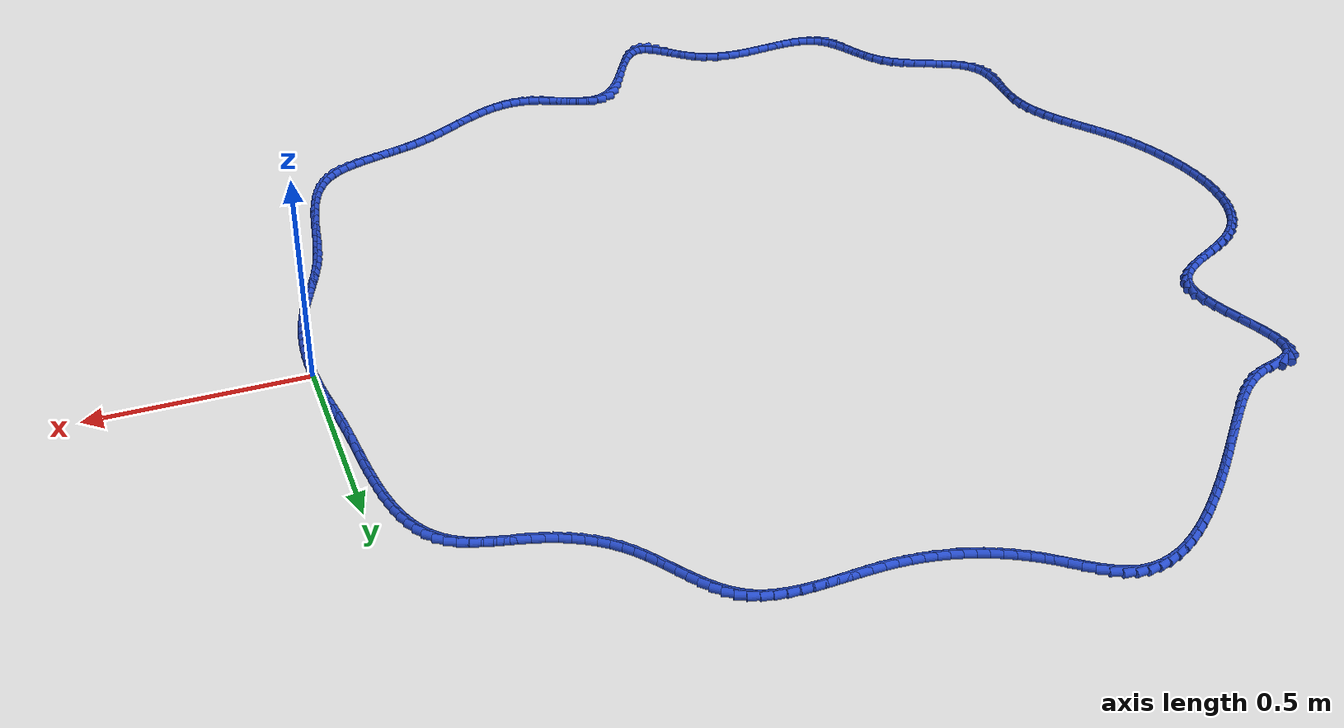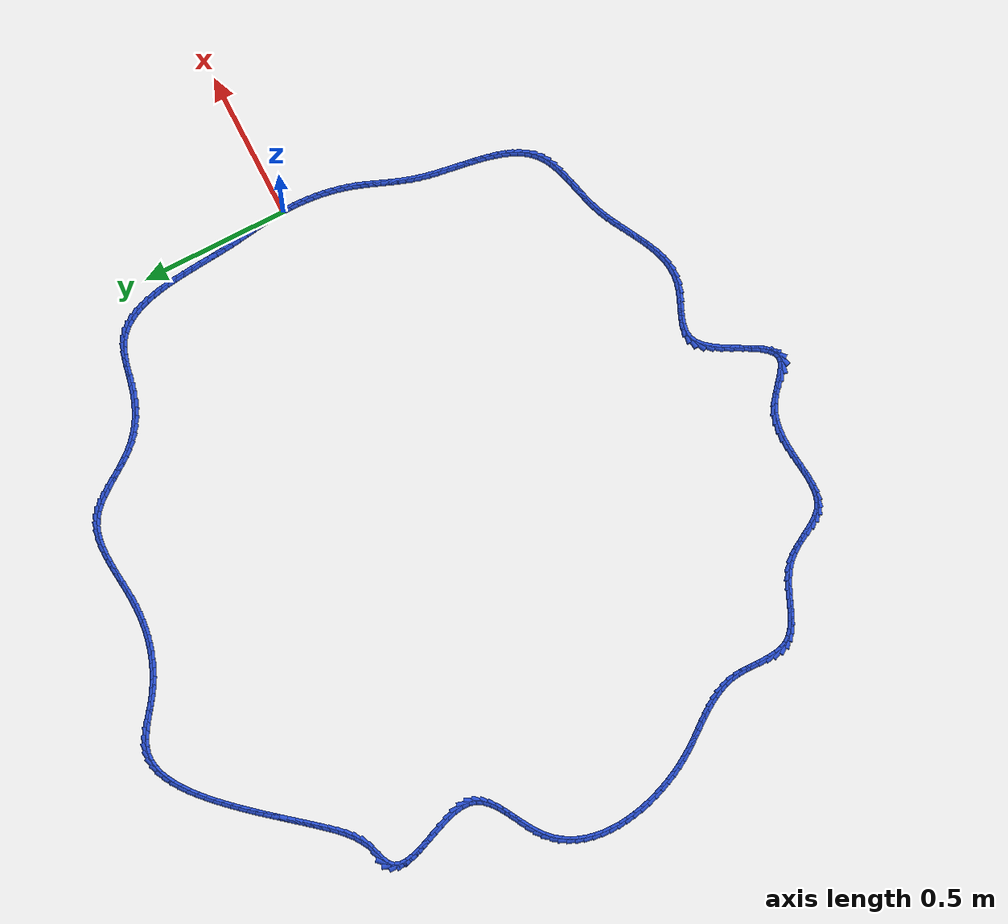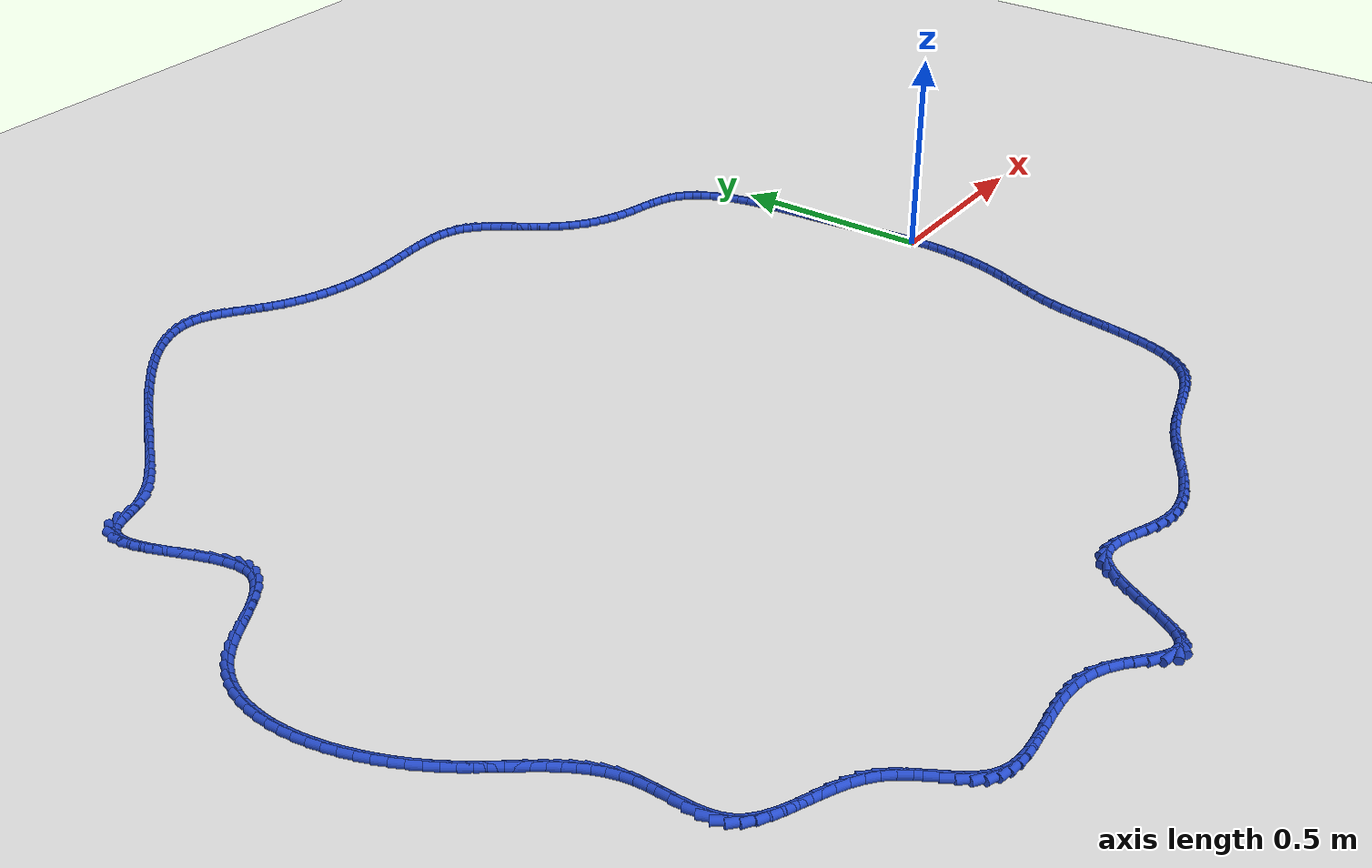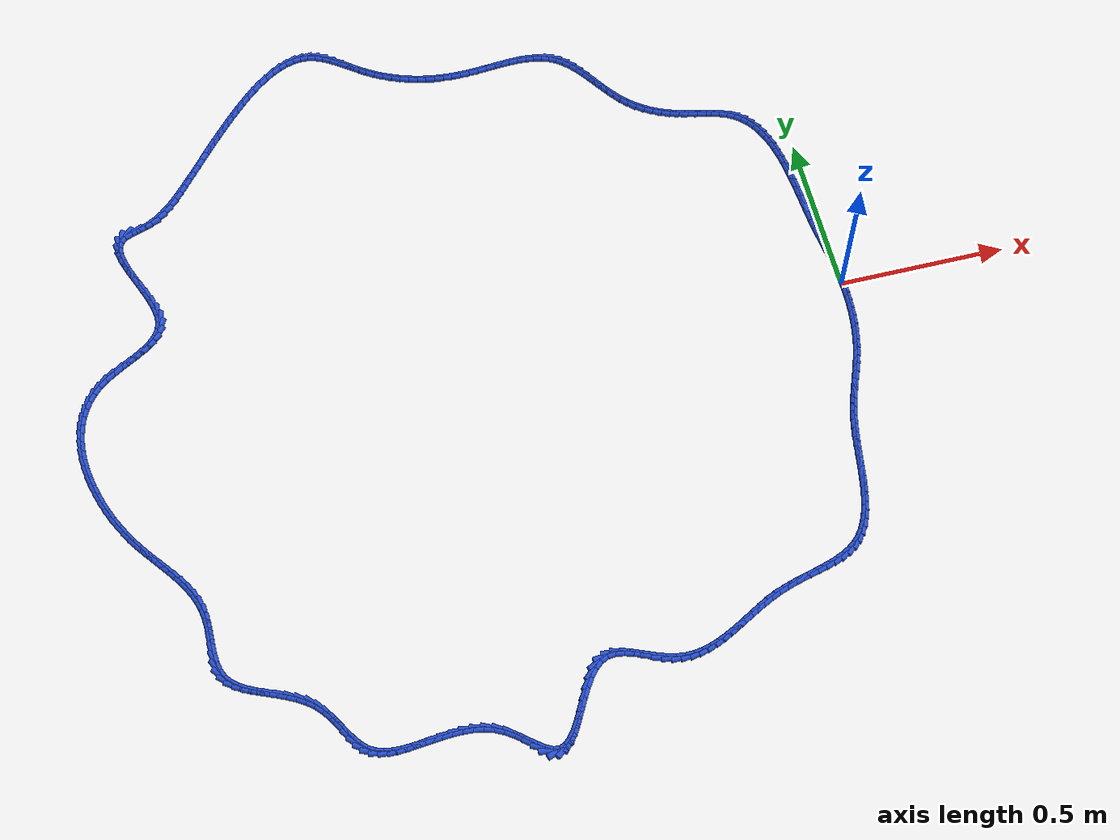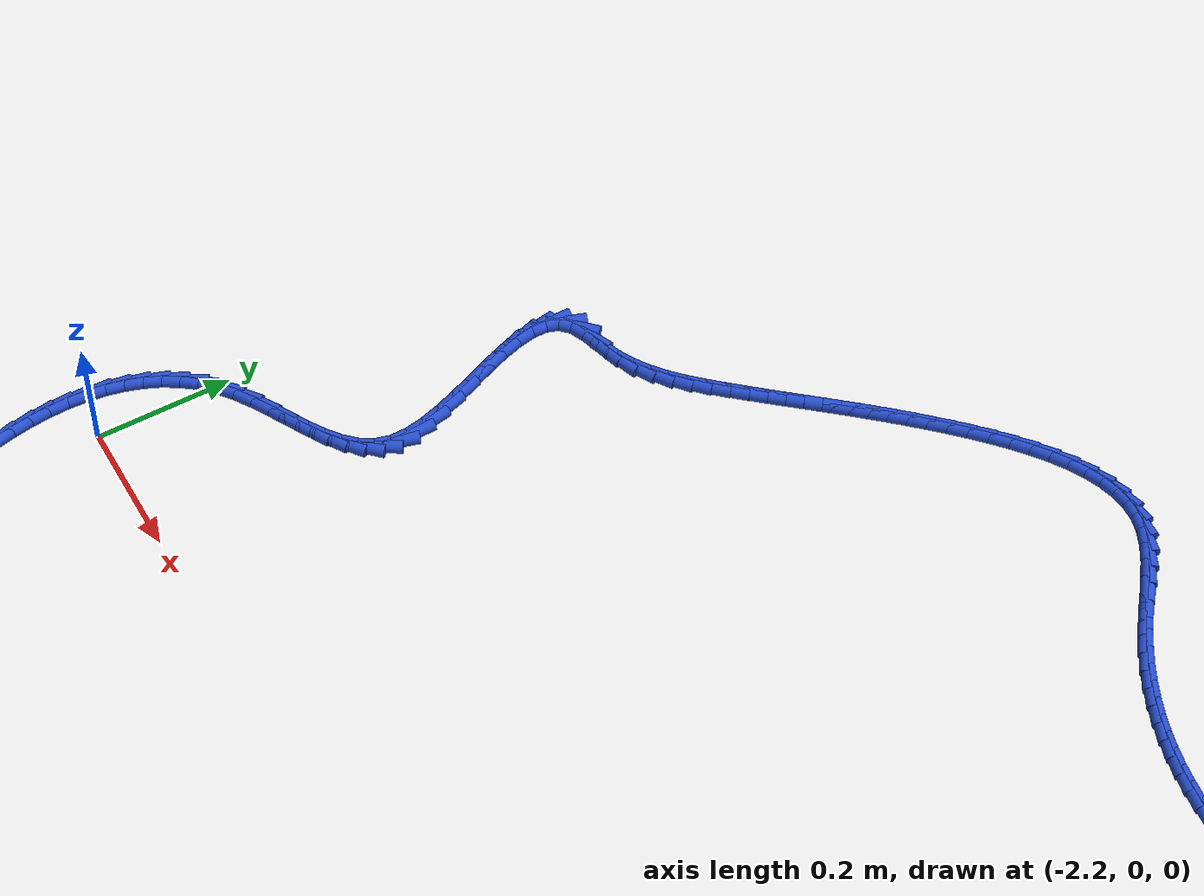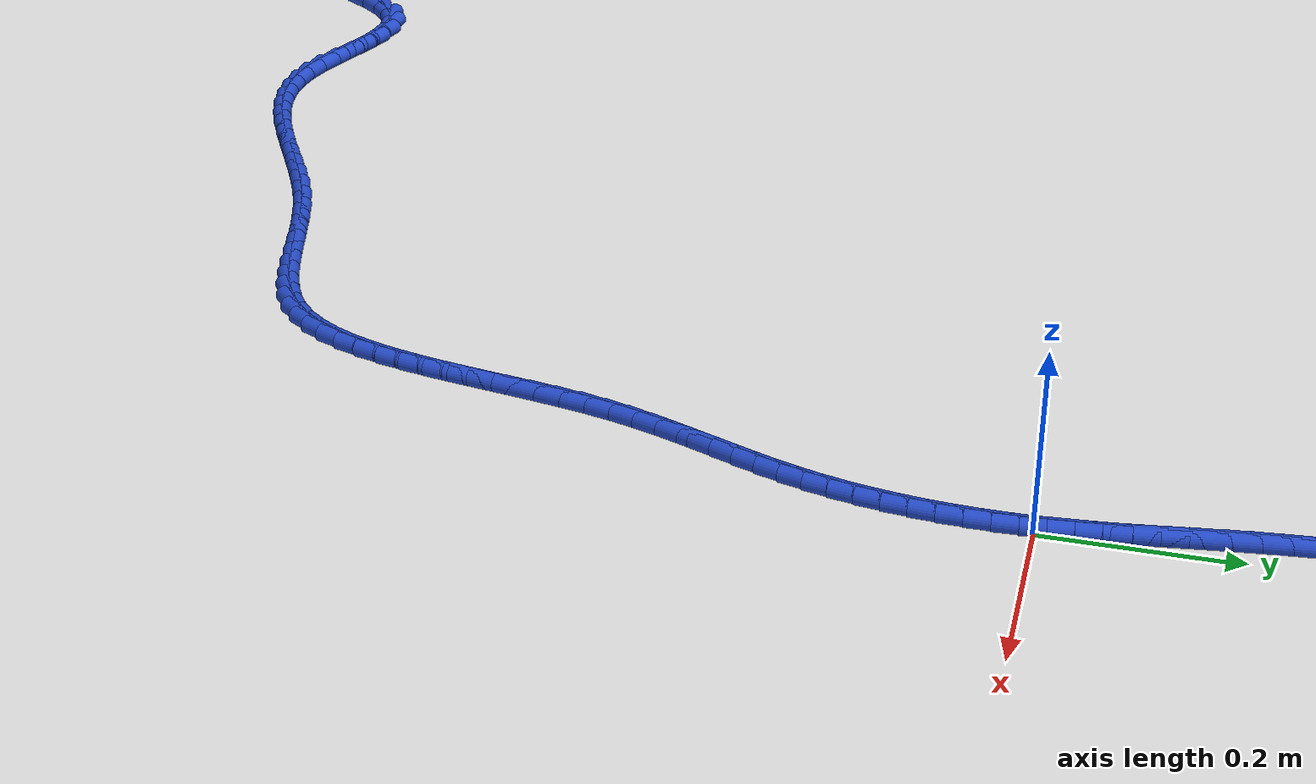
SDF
<sdf version="1.6">
 <world name="default">
  <light name="sun" type="directional">
   <pose>0 0 10 0 -0 0</pose>
   <diffuse>0.8 0.8 0.8 1</diffuse>
   <specular>0.2 0.2 0.2 1</specular>
   <attenuation>
    <range>1000</range>
    <constant>0.9</constant>
    <linear>0.01</linear>
    <quadratic>0.001</quadratic>
   </attenuation>
   <direction>-0.5 0.1 -0.9</direction>
  </light>
  <model name="ground_plane">
   <static>1</static>
   <link name="link">
    <collision name="collision">
     <geometry><plane><normal>0 0 1</normal><size>100 100</size></plane></geometry>
     <surface><friction><ode><mu>100</mu><mu2>50</mu2></ode></friction></surface>
    </collision>
    <visual name="visual">
     <cast_shadows>0</cast_shadows>
     <geometry><plane><normal>0 0 1</normal><size>100 100</size></plane></geometry>
     <material>
      <script><uri>file://media/materials/scripts/gazebo.material</uri><name>Gazebo/WhiteGlow</name></script>
     </material>
    </visual>
   </link>
  </model>
  <gravity>0 0 -9.8</gravity>
  <magnetic_field>6e-06 2.3e-05 -4.2e-05</magnetic_field>
  <atmosphere type="adiabatic"/>
  <physics name="default_physics" default="0" type="ode">
   <max_step_size>0.001</max_step_size>
   <real_time_factor>1</real_time_factor>
   <real_time_update_rate>1000</real_time_update_rate>
  </physics>
  <scene><ambient>0.4 0.4 0.4 1</ambient><background>0.7 0.7 0.7 1</background><shadows>1</shadows></scene>
  <spherical_coordinates>
   <surface_model>EARTH_WGS84</surface_model>
   <latitude_deg>0</latitude_deg>
   <longitude_deg>0</longitude_deg>
   <elevation>0</elevation>
   <heading_deg>0</heading_deg>
  </spherical_coordinates>
  <model name="line">
   <link name="link_0">
    <pose>-8.673617379884035e-19 2.7755575615628914e-17 0.01 0 1.57 -1.5128704500691879</pose>
    <collision name="collision">
     <geometry><cylinder><radius>0.01</radius><length>0.08</length></cylinder></geometry>
    </collision>
    <visual name="visual">
     <material>
      <script><name>Gazebo/Blue</name><uri>file://media/materials/scripts/gazebo.material</uri></script>
     </material>
     <geometry><cylinder><radius>0.01</radius><length>0.08</length></cylinder></geometry>
    </visual>
   </link>
   <link name="link_1">
    <pose>-0.0015045076664612004 0.025943924021290907 0.01 0 1.57 -1.4839128301922735</pose>
    <collision name="collision">
     <geometry><cylinder><radius>0.01</radius><length>0.08</length></cylinder></geometry>
    </collision>
    <visual name="visual">
     <material>
      <script><name>Gazebo/Blue</name><uri>file://media/materials/scripts/gazebo.material</uri></script>
     </material>
     <geometry><cylinder><radius>0.01</radius><length>0.08</length></cylinder></geometry>
    </visual>
   </link>
   <link name="link_2">
    <pose>-0.00374537291131996 0.051670603096480805 0.01 0 1.57 -1.4614351807810255</pose>
    <collision name="collision">
     <geometry><cylinder><radius>0.01</radius><length>0.08</length></cylinder></geometry>
    </collision>
    <visual name="visual">
     <material>
      <script><name>Gazebo/Blue</name><uri>file://media/materials/scripts/gazebo.material</uri></script>
     </material>
     <geometry><cylinder><radius>0.01</radius><length>0.08</length></cylinder></geometry>
    </visual>
   </link>
   <link name="link_3">
    <pose>-0.00656273459518949 0.0773298163537965 0.01 0 1.57 -1.4458176689725841</pose>
    <collision name="collision">
     <geometry><cylinder><radius>0.01</radius><length>0.08</length></cylinder></geometry>
    </collision>
    <visual name="visual">
     <material>
      <script><name>Gazebo/Blue</name><uri>file://media/materials/scripts/gazebo.material</uri></script>
     </material>
     <geometry><cylinder><radius>0.01</radius><length>0.08</length></cylinder></geometry>
    </visual>
   </link>
   <link name="link_4">
    <pose>-0.009796731578683014 0.10307134292146485 0.01 0 1.57 -1.4372000547114856</pose>
    <collision name="collision">
     <geometry><cylinder><radius>0.01</radius><length>0.08</length></cylinder></geometry>
    </collision>
    <visual name="visual">
     <material>
      <script><name>Gazebo/Blue</name><uri>file://media/materials/scripts/gazebo.material</uri></script>
     </material>
     <geometry><cylinder><radius>0.01</radius><length>0.08</length></cylinder></geometry>
    </visual>
   </link>
   <link name="link_5">
    <pose>-0.01328750272241375 0.1290449619277127 0.01 0 1.57 -1.4355012979683903</pose>
    <collision name="collision">
     <geometry><cylinder><radius>0.01</radius><length>0.08</length></cylinder></geometry>
    </collision>
    <visual name="visual">
     <material>
      <script><name>Gazebo/Blue</name><uri>file://media/materials/scripts/gazebo.material</uri></script>
     </material>
     <geometry><cylinder><radius>0.01</radius><length>0.08</length></cylinder></geometry>
    </visual>
   </link>
   <link name="link_6">
    <pose>-0.016875186886994922 0.15540045250076692 0.01 0 1.57 -1.4404459054499166</pose>
    <collision name="collision">
     <geometry><cylinder><radius>0.01</radius><length>0.08</length></cylinder></geometry>
    </collision>
    <visual name="visual">
     <material>
      <script><name>Gazebo/Blue</name><uri>file://media/materials/scripts/gazebo.material</uri></script>
     </material>
     <geometry><cylinder><radius>0.01</radius><length>0.08</length></cylinder></geometry>
    </visual>
   </link>
   <link name="link_7">
    <pose>-0.020399922933039747 0.18228759376885423 0.01 0 1.57 -1.4515927462899783</pose>
    <collision name="collision">
     <geometry><cylinder><radius>0.01</radius><length>0.08</length></cylinder></geometry>
    </collision>
    <visual name="visual">
     <material>
      <script><name>Gazebo/Blue</name><uri>file://media/materials/scripts/gazebo.material</uri></script>
     </material>
     <geometry><cylinder><radius>0.01</radius><length>0.08</length></cylinder></geometry>
    </visual>
   </link>
   <link name="link_8">
    <pose>-0.023701849721161447 0.20985616486020162 0.01 0 1.57 -1.4680017954783229</pose>
    <collision name="collision">
     <geometry><cylinder><radius>0.01</radius><length>0.08</length></cylinder></geometry>
    </collision>
    <visual name="visual">
     <material>
      <script><name>Gazebo/Blue</name><uri>file://media/materials/scripts/gazebo.material</uri></script>
     </material>
     <geometry><cylinder><radius>0.01</radius><length>0.08</length></cylinder></geometry>
    </visual>
   </link>
   <link name="link_9">
    <pose>-0.026630461227368025 0.23824570004829687 0.01 0 1.57 -1.4826673577062643</pose>
    <collision name="collision">
     <geometry><cylinder><radius>0.01</radius><length>0.08</length></cylinder></geometry>
    </collision>
    <visual name="visual">
     <material>
      <script><name>Gazebo/Blue</name><uri>file://media/materials/scripts/gazebo.material</uri></script>
     </material>
     <geometry><cylinder><radius>0.01</radius><length>0.08</length></cylinder></geometry>
    </visual>
   </link>
   <link name="link_10">
    <pose>-0.0292071350444242 0.26740750261092483 0.01 0 1.57 -1.4903211158012812</pose>
    <collision name="collision">
     <geometry><cylinder><radius>0.01</radius><length>0.08</length></cylinder></geometry>
    </collision>
    <visual name="visual">
     <material>
      <script><name>Gazebo/Blue</name><uri>file://media/materials/scripts/gazebo.material</uri></script>
     </material>
     <geometry><cylinder><radius>0.01</radius><length>0.08</length></cylinder></geometry>
    </visual>
   </link>
   <link name="link_11">
    <pose>-0.03160405311483432 0.29712772888840494 0.01 0 1.57 -1.4913060136320955</pose>
    <collision name="collision">
     <geometry><cylinder><radius>0.01</radius><length>0.08</length></cylinder></geometry>
    </collision>
    <visual name="visual">
     <material>
      <script><name>Gazebo/Blue</name><uri>file://media/materials/scripts/gazebo.material</uri></script>
     </material>
     <geometry><cylinder><radius>0.01</radius><length>0.08</length></cylinder></geometry>
    </visual>
   </link>
   <link name="link_12">
    <pose>-0.033998514007887996 0.3271869319659438 0.01 0 1.57 -1.4858649426653563</pose>
    <collision name="collision">
     <geometry><cylinder><radius>0.01</radius><length>0.08</length></cylinder></geometry>
    </collision>
    <visual name="visual">
     <material>
      <script><name>Gazebo/Blue</name><uri>file://media/materials/scripts/gazebo.material</uri></script>
     </material>
     <geometry><cylinder><radius>0.01</radius><length>0.08</length></cylinder></geometry>
    </visual>
   </link>
   <link name="link_13">
    <pose>-0.036567816292874825 0.35736566492874766 0.01 0 1.57 -1.4739737849723542</pose>
    <collision name="collision">
     <geometry><cylinder><radius>0.01</radius><length>0.08</length></cylinder></geometry>
    </collision>
    <visual name="visual">
     <material>
      <script><name>Gazebo/Blue</name><uri>file://media/materials/scripts/gazebo.material</uri></script>
     </material>
     <geometry><cylinder><radius>0.01</radius><length>0.08</length></cylinder></geometry>
    </visual>
   </link>
   <link name="link_14">
    <pose>-0.03948925853908443 0.3874444808620231 0.01 0 1.57 -1.4553527718935229</pose>
    <collision name="collision">
     <geometry><cylinder><radius>0.01</radius><length>0.08</length></cylinder></geometry>
    </collision>
    <visual name="visual">
     <material>
      <script><name>Gazebo/Blue</name><uri>file://media/materials/scripts/gazebo.material</uri></script>
     </material>
     <geometry><cylinder><radius>0.01</radius><length>0.08</length></cylinder></geometry>
    </visual>
   </link>
   <link name="link_15">
    <pose>-0.042940139315806404 0.4172039328509768 0.01 0 1.57 -1.4294613938874563</pose>
    <collision name="collision">
     <geometry><cylinder><radius>0.01</radius><length>0.08</length></cylinder></geometry>
    </collision>
    <visual name="visual">
     <material>
      <script><name>Gazebo/Blue</name><uri>file://media/materials/scripts/gazebo.material</uri></script>
     </material>
     <geometry><cylinder><radius>0.01</radius><length>0.08</length></cylinder></geometry>
    </visual>
   </link>
   <link name="link_16">
    <pose>-0.04709775719233038 0.44642457398081503 0.01 0 1.57 -1.3954809023266712</pose>
    <collision name="collision">
     <geometry><cylinder><radius>0.01</radius><length>0.08</length></cylinder></geometry>
    </collision>
    <visual name="visual">
     <material>
      <script><name>Gazebo/Blue</name><uri>file://media/materials/scripts/gazebo.material</uri></script>
     </material>
     <geometry><cylinder><radius>0.01</radius><length>0.08</length></cylinder></geometry>
    </visual>
   </link>
   <link name="link_17">
    <pose>-0.05213941073794594 0.4748869573367444 0.01 0 1.57 -1.3522909883934888</pose>
    <collision name="collision">
     <geometry><cylinder><radius>0.01</radius><length>0.08</length></cylinder></geometry>
    </collision>
    <visual name="visual">
     <material>
      <script><name>Gazebo/Blue</name><uri>file://media/materials/scripts/gazebo.material</uri></script>
     </material>
     <geometry><cylinder><radius>0.01</radius><length>0.08</length></cylinder></geometry>
    </visual>
   </link>
   <link name="link_18">
    <pose>-0.05824239852194268 0.5023716360039712 0.01 0 1.57 -1.2984539915197313</pose>
    <collision name="collision">
     <geometry><cylinder><radius>0.01</radius><length>0.08</length></cylinder></geometry>
    </collision>
    <visual name="visual">
     <material>
      <script><name>Gazebo/Blue</name><uri>file://media/materials/scripts/gazebo.material</uri></script>
     </material>
     <geometry><cylinder><radius>0.01</radius><length>0.08</length></cylinder></geometry>
    </visual>
   </link>
   <link name="link_19">
    <pose>-0.06558401911361023 0.528659163067702 0.01 0 1.57 -1.2322340940447465</pose>
    <collision name="collision">
     <geometry><cylinder><radius>0.01</radius><length>0.08</length></cylinder></geometry>
    </collision>
    <visual name="visual">
     <material>
      <script><name>Gazebo/Blue</name><uri>file://media/materials/scripts/gazebo.material</uri></script>
     </material>
     <geometry><cylinder><radius>0.01</radius><length>0.08</length></cylinder></geometry>
    </visual>
   </link>
   <link name="link_20">
    <pose>-0.07434157108223821 0.5535300916131435 0.01 0 1.57 -1.1517037740447187</pose>
    <collision name="collision">
     <geometry><cylinder><radius>0.01</radius><length>0.08</length></cylinder></geometry>
    </collision>
    <visual name="visual">
     <material>
      <script><name>Gazebo/Blue</name><uri>file://media/materials/scripts/gazebo.material</uri></script>
     </material>
     <geometry><cylinder><radius>0.01</radius><length>0.08</length></cylinder></geometry>
    </visual>
   </link>
   <link name="link_21">
    <pose>-0.08469235299711621 0.5767649747255019 0.01 0 1.57 -1.0550235052395125</pose>
    <collision name="collision">
     <geometry><cylinder><radius>0.01</radius><length>0.08</length></cylinder></geometry>
    </collision>
    <visual name="visual">
     <material>
      <script><name>Gazebo/Blue</name><uri>file://media/materials/scripts/gazebo.material</uri></script>
     </material>
     <geometry><cylinder><radius>0.01</radius><length>0.08</length></cylinder></geometry>
    </visual>
   </link>
   <link name="link_22">
    <pose>-0.09681366342753381 0.5981443654899837 0.01 0 1.57 -0.9410000450630925</pose>
    <collision name="collision">
     <geometry><cylinder><radius>0.01</radius><length>0.08</length></cylinder></geometry>
    </collision>
    <visual name="visual">
     <material>
      <script><name>Gazebo/Blue</name><uri>file://media/materials/scripts/gazebo.material</uri></script>
     </material>
     <geometry><cylinder><radius>0.01</radius><length>0.08</length></cylinder></geometry>
    </visual>
   </link>
   <link name="link_23">
    <pose>-0.11088280094278062 0.6174488169917955 0.01 0 1.57 -0.8099623723508368</pose>
    <collision name="collision">
     <geometry><cylinder><radius>0.01</radius><length>0.08</length></cylinder></geometry>
    </collision>
    <visual name="visual">
     <material>
      <script><name>Gazebo/Blue</name><uri>file://media/materials/scripts/gazebo.material</uri></script>
     </material>
     <geometry><cylinder><radius>0.01</radius><length>0.08</length></cylinder></geometry>
    </visual>
   </link>
   <link name="link_24">
    <pose>-0.12707706411214637 0.6344588823161439 0.01 0 1.57 -0.6647352632352869</pose>
    <collision name="collision">
     <geometry><cylinder><radius>0.01</radius><length>0.08</length></cylinder></geometry>
    </collision>
    <visual name="visual">
     <material>
      <script><name>Gazebo/Blue</name><uri>file://media/materials/scripts/gazebo.material</uri></script>
     </material>
     <geometry><cylinder><radius>0.01</radius><length>0.08</length></cylinder></geometry>
    </visual>
   </link>
   <link name="link_25">
    <pose>-0.14557375150492047 0.6489551145482352 0.01 0 1.57 -0.5120050205259337</pose>
    <collision name="collision">
     <geometry><cylinder><radius>0.01</radius><length>0.08</length></cylinder></geometry>
    </collision>
    <visual name="visual">
     <material>
      <script><name>Gazebo/Blue</name><uri>file://media/materials/scripts/gazebo.material</uri></script>
     </material>
     <geometry><cylinder><radius>0.01</radius><length>0.08</length></cylinder></geometry>
    </visual>
   </link>
   <link name="link_26">
    <pose>-0.16653618931143183 0.6607358794592619 0.01 0 1.57 -0.38060713266687035</pose>
    <collision name="collision">
     <geometry><cylinder><radius>0.01</radius><length>0.08</length></cylinder></geometry>
    </collision>
    <visual name="visual">
     <material>
      <script><name>Gazebo/Blue</name><uri>file://media/materials/scripts/gazebo.material</uri></script>
     </material>
     <geometry><cylinder><radius>0.01</radius><length>0.08</length></cylinder></geometry>
    </visual>
   </link>
   <link name="link_27">
    <pose>-0.18978399552947572 0.6700377191769027 0.01 0 1.57 -0.29201493422989855</pose>
    <collision name="collision">
     <geometry><cylinder><radius>0.01</radius><length>0.08</length></cylinder></geometry>
    </collision>
    <visual name="visual">
     <material>
      <script><name>Gazebo/Blue</name><uri>file://media/materials/scripts/gazebo.material</uri></script>
     </material>
     <geometry><cylinder><radius>0.01</radius><length>0.08</length></cylinder></geometry>
    </visual>
   </link>
   <link name="link_28">
    <pose>-0.21478018866431217 0.6775517866578992 0.01 0 1.57 -0.24105027184352956</pose>
    <collision name="collision">
     <geometry><cylinder><radius>0.01</radius><length>0.08</length></cylinder></geometry>
    </collision>
    <visual name="visual">
     <material>
      <script><name>Gazebo/Blue</name><uri>file://media/materials/scripts/gazebo.material</uri></script>
     </material>
     <geometry><cylinder><radius>0.01</radius><length>0.08</length></cylinder></geometry>
    </visual>
   </link>
   <link name="link_29">
    <pose>-0.2409712354864395 0.6839903358364767 0.01 0 1.57 -0.22266206944576403</pose>
    <collision name="collision">
     <geometry><cylinder><radius>0.01</radius><length>0.08</length></cylinder></geometry>
    </collision>
    <visual name="visual">
     <material>
      <script><name>Gazebo/Blue</name><uri>file://media/materials/scripts/gazebo.material</uri></script>
     </material>
     <geometry><cylinder><radius>0.01</radius><length>0.08</length></cylinder></geometry>
    </visual>
   </link>
   <link name="link_30">
    <pose>-0.26780360276635584 0.6900656206468609 0.01 0 1.57 -0.23426036577206738</pose>
    <collision name="collision">
     <geometry><cylinder><radius>0.01</radius><length>0.08</length></cylinder></geometry>
    </collision>
    <visual name="visual">
     <material>
      <script><name>Gazebo/Blue</name><uri>file://media/materials/scripts/gazebo.material</uri></script>
     </material>
     <geometry><cylinder><radius>0.01</radius><length>0.08</length></cylinder></geometry>
    </visual>
   </link>
   <link name="link_31">
    <pose>-0.2947237572745594 0.6964898950232765 0.01 0 1.57 -0.27562030793661396</pose>
    <collision name="collision">
     <geometry><cylinder><radius>0.01</radius><length>0.08</length></cylinder></geometry>
    </collision>
    <visual name="visual">
     <material>
      <script><name>Gazebo/Blue</name><uri>file://media/materials/scripts/gazebo.material</uri></script>
     </material>
     <geometry><cylinder><radius>0.01</radius><length>0.08</length></cylinder></geometry>
    </visual>
   </link>
   <link name="link_32">
    <pose>-0.3211803999460942 0.7039723209563044 0.01 0 1.57 -0.33871883276390063</pose>
    <collision name="collision">
     <geometry><cylinder><radius>0.01</radius><length>0.08</length></cylinder></geometry>
    </collision>
    <visual name="visual">
     <material>
      <script><name>Gazebo/Blue</name><uri>file://media/materials/scripts/gazebo.material</uri></script>
     </material>
     <geometry><cylinder><radius>0.01</radius><length>0.08</length></cylinder></geometry>
    </visual>
   </link>
   <link name="link_33">
    <pose>-0.3467873492805759 0.7129935480803647 0.01 0 1.57 -0.4081915126884785</pose>
    <collision name="collision">
     <geometry><cylinder><radius>0.01</radius><length>0.08</length></cylinder></geometry>
    </collision>
    <visual name="visual">
     <material>
      <script><name>Gazebo/Blue</name><uri>file://media/materials/scripts/gazebo.material</uri></script>
     </material>
     <geometry><cylinder><radius>0.01</radius><length>0.08</length></cylinder></geometry>
    </visual>
   </link>
   <link name="link_34">
    <pose>-0.37143402526774894 0.7236528108483139 0.01 0 1.57 -0.482426022428486</pose>
    <collision name="collision">
     <geometry><cylinder><radius>0.01</radius><length>0.08</length></cylinder></geometry>
    </collision>
    <visual name="visual">
     <material>
      <script><name>Gazebo/Blue</name><uri>file://media/materials/scripts/gazebo.material</uri></script>
     </material>
     <geometry><cylinder><radius>0.01</radius><length>0.08</length></cylinder></geometry>
    </visual>
   </link>
   <link name="link_35">
    <pose>-0.39503601347039424 0.7360131322005602 0.01 0 1.57 -0.5611184005027752</pose>
    <collision name="collision">
     <geometry><cylinder><radius>0.01</radius><length>0.08</length></cylinder></geometry>
    </collision>
    <visual name="visual">
     <material>
      <script><name>Gazebo/Blue</name><uri>file://media/materials/scripts/gazebo.material</uri></script>
     </material>
     <geometry><cylinder><radius>0.01</radius><length>0.08</length></cylinder></geometry>
    </visual>
   </link>
   <link name="link_36">
    <pose>-0.41750889945129255 0.7501375350775114 0.01 0 1.57 -0.6437112147604783</pose>
    <collision name="collision">
     <geometry><cylinder><radius>0.01</radius><length>0.08</length></cylinder></geometry>
    </collision>
    <visual name="visual">
     <material>
      <script><name>Gazebo/Blue</name><uri>file://media/materials/scripts/gazebo.material</uri></script>
     </material>
     <geometry><cylinder><radius>0.01</radius><length>0.08</length></cylinder></geometry>
    </visual>
   </link>
   <link name="link_37">
    <pose>-0.4387682687732251 0.7660890424195755 0.01 0 1.57 -0.72938192817124</pose>
    <collision name="collision">
     <geometry><cylinder><radius>0.01</radius><length>0.08</length></cylinder></geometry>
    </collision>
    <visual name="visual">
     <material>
      <script><name>Gazebo/Blue</name><uri>file://media/materials/scripts/gazebo.material</uri></script>
     </material>
     <geometry><cylinder><radius>0.01</radius><length>0.08</length></cylinder></geometry>
    </visual>
   </link>
   <link name="link_38">
    <pose>-0.4587297069989729 0.7839306771671614 0.01 0 1.57 -0.8158420235107297</pose>
    <collision name="collision">
     <geometry><cylinder><radius>0.01</radius><length>0.08</length></cylinder></geometry>
    </collision>
    <visual name="visual">
     <material>
      <script><name>Gazebo/Blue</name><uri>file://media/materials/scripts/gazebo.material</uri></script>
     </material>
     <geometry><cylinder><radius>0.01</radius><length>0.08</length></cylinder></geometry>
    </visual>
   </link>
   <link name="link_39">
    <pose>-0.4773277044500205 0.8036969933828818 0.01 0 1.57 -0.8875729127625017</pose>
    <collision name="collision">
     <geometry><cylinder><radius>0.01</radius><length>0.08</length></cylinder></geometry>
    </collision>
    <visual name="visual">
     <material>
      <script><name>Gazebo/Blue</name><uri>file://media/materials/scripts/gazebo.material</uri></script>
     </material>
     <geometry><cylinder><radius>0.01</radius><length>0.08</length></cylinder></geometry>
    </visual>
   </link>
   <link name="link_40">
    <pose>-0.49472843956770457 0.8250736435181769 0.01 0 1.57 -0.9360237430965254</pose>
    <collision name="collision">
     <geometry><cylinder><radius>0.01</radius><length>0.08</length></cylinder></geometry>
    </collision>
    <visual name="visual">
     <material>
      <script><name>Gazebo/Blue</name><uri>file://media/materials/scripts/gazebo.material</uri></script>
     </material>
     <geometry><cylinder><radius>0.01</radius><length>0.08</length></cylinder></geometry>
    </visual>
   </link>
   <link name="link_41">
    <pose>-0.5112534290885703 0.8475123544286918 0.01 0 1.57 -0.9627103448253748</pose>
    <collision name="collision">
     <geometry><cylinder><radius>0.01</radius><length>0.08</length></cylinder></geometry>
    </collision>
    <visual name="visual">
     <material>
      <script><name>Gazebo/Blue</name><uri>file://media/materials/scripts/gazebo.material</uri></script>
     </material>
     <geometry><cylinder><radius>0.01</radius><length>0.08</length></cylinder></geometry>
    </visual>
   </link>
   <link name="link_42">
    <pose>-0.5272270553042055 0.8704605377001627 0.01 0 1.57 -0.9685264278891036</pose>
    <collision name="collision">
     <geometry><cylinder><radius>0.01</radius><length>0.08</length></cylinder></geometry>
    </collision>
    <visual name="visual">
     <material>
      <script><name>Gazebo/Blue</name><uri>file://media/materials/scripts/gazebo.material</uri></script>
     </material>
     <geometry><cylinder><radius>0.01</radius><length>0.08</length></cylinder></geometry>
    </visual>
   </link>
   <link name="link_43">
    <pose>-0.5429737005061991 0.8933656049183274 0.01 0 1.57 -0.9532593532250917</pose>
    <collision name="collision">
     <geometry><cylinder><radius>0.01</radius><length>0.08</length></cylinder></geometry>
    </collision>
    <visual name="visual">
     <material>
      <script><name>Gazebo/Blue</name><uri>file://media/materials/scripts/gazebo.material</uri></script>
     </material>
     <geometry><cylinder><radius>0.01</radius><length>0.08</length></cylinder></geometry>
    </visual>
   </link>
   <link name="link_44">
    <pose>-0.5588177469861391 0.9156749676689233 0.01 0 1.57 -0.9154545720699168</pose>
    <collision name="collision">
     <geometry><cylinder><radius>0.01</radius><length>0.08</length></cylinder></geometry>
    </collision>
    <visual name="visual">
     <material>
      <script><name>Gazebo/Blue</name><uri>file://media/materials/scripts/gazebo.material</uri></script>
     </material>
     <geometry><cylinder><radius>0.01</radius><length>0.08</length></cylinder></geometry>
    </visual>
   </link>
   <link name="link_45">
    <pose>-0.575083577035614 0.9368360375376873 0.01 0 1.57 -0.852422544290583</pose>
    <collision name="collision">
     <geometry><cylinder><radius>0.01</radius><length>0.08</length></cylinder></geometry>
    </collision>
    <visual name="visual">
     <material>
      <script><name>Gazebo/Blue</name><uri>file://media/materials/scripts/gazebo.material</uri></script>
     </material>
     <geometry><cylinder><radius>0.01</radius><length>0.08</length></cylinder></geometry>
    </visual>
   </link>
   <link name="link_46">
    <pose>-0.5920955729462122 0.9562962261103565 0.01 0 1.57 -0.7605847960566386</pose>
    <collision name="collision">
     <geometry><cylinder><radius>0.01</radius><length>0.08</length></cylinder></geometry>
    </collision>
    <visual name="visual">
     <material>
      <script><name>Gazebo/Blue</name><uri>file://media/materials/scripts/gazebo.material</uri></script>
     </material>
     <geometry><cylinder><radius>0.01</radius><length>0.08</length></cylinder></geometry>
    </visual>
   </link>
   <link name="link_47">
    <pose>-0.6101781170095215 0.9735029449726681 0.01 0 1.57 -0.6366498602851868</pose>
    <collision name="collision">
     <geometry><cylinder><radius>0.01</radius><length>0.08</length></cylinder></geometry>
    </collision>
    <visual name="visual">
     <material>
      <script><name>Gazebo/Blue</name><uri>file://media/materials/scripts/gazebo.material</uri></script>
     </material>
     <geometry><cylinder><radius>0.01</radius><length>0.08</length></cylinder></geometry>
    </visual>
   </link>
   <link name="link_48">
    <pose>-0.6296555915171309 0.9879036057103594 0.01 0 1.57 -0.4834918458057998</pose>
    <collision name="collision">
     <geometry><cylinder><radius>0.01</radius><length>0.08</length></cylinder></geometry>
    </collision>
    <visual name="visual">
     <material>
      <script><name>Gazebo/Blue</name><uri>file://media/materials/scripts/gazebo.material</uri></script>
     </material>
     <geometry><cylinder><radius>0.01</radius><length>0.08</length></cylinder></geometry>
    </visual>
   </link>
   <link name="link_49">
    <pose>-0.6508155661732381 0.9990138028776434 0.01 0 1.57 -0.3348806330257192</pose>
    <collision name="collision">
     <geometry><cylinder><radius>0.01</radius><length>0.08</length></cylinder></geometry>
    </collision>
    <visual name="visual">
     <material>
      <script><name>Gazebo/Blue</name><uri>file://media/materials/scripts/gazebo.material</uri></script>
     </material>
     <geometry><cylinder><radius>0.01</radius><length>0.08</length></cylinder></geometry>
    </visual>
   </link>
   <link name="link_50">
    <pose>-0.6736212542924794 1.0069498924272768 0.01 0 1.57 -0.21090569408652016</pose>
    <collision name="collision">
     <geometry><cylinder><radius>0.01</radius><length>0.08</length></cylinder></geometry>
    </collision>
    <visual name="visual">
     <material>
      <script><name>Gazebo/Blue</name><uri>file://media/materials/scripts/gazebo.material</uri></script>
     </material>
     <geometry><cylinder><radius>0.01</radius><length>0.08</length></cylinder></geometry>
    </visual>
   </link>
   <link name="link_51">
    <pose>-0.6978671706627564 1.0121406877388295 0.01 0 1.57 -0.11243899534678568</pose>
    <collision name="collision">
     <geometry><cylinder><radius>0.01</radius><length>0.08</length></cylinder></geometry>
    </collision>
    <visual name="visual">
     <material>
      <script><name>Gazebo/Blue</name><uri>file://media/materials/scripts/gazebo.material</uri></script>
     </material>
     <geometry><cylinder><radius>0.01</radius><length>0.08</length></cylinder></geometry>
    </visual>
   </link>
   <link name="link_52">
    <pose>-0.7233463846549669 1.0150176793419718 0.01 0 1.57 -0.03750953011272407</pose>
    <collision name="collision">
     <geometry><cylinder><radius>0.01</radius><length>0.08</length></cylinder></geometry>
    </collision>
    <visual name="visual">
     <material>
      <script><name>Gazebo/Blue</name><uri>file://media/materials/scripts/gazebo.material</uri></script>
     </material>
     <geometry><cylinder><radius>0.01</radius><length>0.08</length></cylinder></geometry>
    </visual>
   </link>
   <link name="link_53">
    <pose>-0.7498519656400087 1.0160123577663738 0.01 0 1.57 0.016691731805753937</pose>
    <collision name="collision">
     <geometry><cylinder><radius>0.01</radius><length>0.08</length></cylinder></geometry>
    </collision>
    <visual name="visual">
     <material>
      <script><name>Gazebo/Blue</name><uri>file://media/materials/scripts/gazebo.material</uri></script>
     </material>
     <geometry><cylinder><radius>0.01</radius><length>0.08</length></cylinder></geometry>
    </visual>
   </link>
   <link name="link_54">
    <pose>-0.7771769829887794 1.0155562135417049 0.01 0 1.57 0.052764405878739776</pose>
    <collision name="collision">
     <geometry><cylinder><radius>0.01</radius><length>0.08</length></cylinder></geometry>
    </collision>
    <visual name="visual">
     <material>
      <script><name>Gazebo/Blue</name><uri>file://media/materials/scripts/gazebo.material</uri></script>
     </material>
     <geometry><cylinder><radius>0.01</radius><length>0.08</length></cylinder></geometry>
    </visual>
   </link>
   <link name="link_55">
    <pose>-0.8051145060721775 1.0140807371976355 0.01 0 1.57 0.07266970575021672</pose>
    <collision name="collision">
     <geometry><cylinder><radius>0.01</radius><length>0.08</length></cylinder></geometry>
    </collision>
    <visual name="visual">
     <material>
      <script><name>Gazebo/Blue</name><uri>file://media/materials/scripts/gazebo.material</uri></script>
     </material>
     <geometry><cylinder><radius>0.01</radius><length>0.08</length></cylinder></geometry>
    </visual>
   </link>
   <link name="link_56">
    <pose>-0.8334576042611003 1.0120174192638356 0.01 0 1.57 0.07761299995104612</pose>
    <collision name="collision">
     <geometry><cylinder><radius>0.01</radius><length>0.08</length></cylinder></geometry>
    </collision>
    <visual name="visual">
     <material>
      <script><name>Gazebo/Blue</name><uri>file://media/materials/scripts/gazebo.material</uri></script>
     </material>
     <geometry><cylinder><radius>0.01</radius><length>0.08</length></cylinder></geometry>
    </visual>
   </link>
   <link name="link_57">
    <pose>-0.8619993469264459 1.0097977502699749 0.01 0 1.57 0.0680438963883847</pose>
    <collision name="collision">
     <geometry><cylinder><radius>0.01</radius><length>0.08</length></cylinder></geometry>
    </collision>
    <visual name="visual">
     <material>
      <script><name>Gazebo/Blue</name><uri>file://media/materials/scripts/gazebo.material</uri></script>
     </material>
     <geometry><cylinder><radius>0.01</radius><length>0.08</length></cylinder></geometry>
    </visual>
   </link>
   <link name="link_58">
    <pose>-0.8905328034391122 1.0078532207457238 0.01 0 1.57 0.04368604610397031</pose>
    <collision name="collision">
     <geometry><cylinder><radius>0.01</radius><length>0.08</length></cylinder></geometry>
    </collision>
    <visual name="visual">
     <material>
      <script><name>Gazebo/Blue</name><uri>file://media/materials/scripts/gazebo.material</uri></script>
     </material>
     <geometry><cylinder><radius>0.01</radius><length>0.08</length></cylinder></geometry>
    </visual>
   </link>
   <link name="link_59">
    <pose>-0.9188510431699966 1.0066153212207514 0.01 0 1.57 0.004650970503568332</pose>
    <collision name="collision">
     <geometry><cylinder><radius>0.01</radius><length>0.08</length></cylinder></geometry>
    </collision>
    <visual name="visual">
     <material>
      <script><name>Gazebo/Blue</name><uri>file://media/materials/scripts/gazebo.material</uri></script>
     </material>
     <geometry><cylinder><radius>0.01</radius><length>0.08</length></cylinder></geometry>
    </visual>
   </link>
   <link name="link_60">
    <pose>-0.9467628874199434 1.0064855031203888 0.01 0 1.57 -0.040977681511806634</pose>
    <collision name="collision">
     <geometry><cylinder><radius>0.01</radius><length>0.08</length></cylinder></geometry>
    </collision>
    <visual name="visual">
     <material>
      <script><name>Gazebo/Blue</name><uri>file://media/materials/scripts/gazebo.material</uri></script>
     </material>
     <geometry><cylinder><radius>0.01</radius><length>0.08</length></cylinder></geometry>
    </visual>
   </link>
   <link name="link_61">
    <pose>-0.9742105306042603 1.0076108738679797 0.01 0 1.57 -0.08866702646823589</pose>
    <collision name="collision">
     <geometry><cylinder><radius>0.01</radius><length>0.08</length></cylinder></geometry>
    </collision>
    <visual name="visual">
     <material>
      <script><name>Gazebo/Blue</name><uri>file://media/materials/scripts/gazebo.material</uri></script>
     </material>
     <geometry><cylinder><radius>0.01</radius><length>0.08</length></cylinder></geometry>
    </visual>
   </link>
   <link name="link_62">
    <pose>-1.001203291697937 1.0100105336103644 0.01 0 1.57 -0.1381868890879453</pose>
    <collision name="collision">
     <geometry><cylinder><radius>0.01</radius><length>0.08</length></cylinder></geometry>
    </collision>
    <visual name="visual">
     <material>
      <script><name>Gazebo/Blue</name><uri>file://media/materials/scripts/gazebo.material</uri></script>
     </material>
     <geometry><cylinder><radius>0.01</radius><length>0.08</length></cylinder></geometry>
    </visual>
   </link>
   <link name="link_63">
    <pose>-1.0277509998403795 1.0137026096052106 0.01 0 1.57 -0.18928607457031812</pose>
    <collision name="collision">
     <geometry><cylinder><radius>0.01</radius><length>0.08</length></cylinder></geometry>
    </collision>
    <visual name="visual">
     <material>
      <script><name>Gazebo/Blue</name><uri>file://media/materials/scripts/gazebo.material</uri></script>
     </material>
     <geometry><cylinder><radius>0.01</radius><length>0.08</length></cylinder></geometry>
    </visual>
   </link>
   <link name="link_64">
    <pose>-1.0538634841709917 1.0187052291101863 0.01 0 1.57 -0.24166065429069838</pose>
    <collision name="collision">
     <geometry><cylinder><radius>0.01</radius><length>0.08</length></cylinder></geometry>
    </collision>
    <visual name="visual">
     <material>
      <script><name>Gazebo/Blue</name><uri>file://media/materials/scripts/gazebo.material</uri></script>
     </material>
     <geometry><cylinder><radius>0.01</radius><length>0.08</length></cylinder></geometry>
    </visual>
   </link>
   <link name="link_65">
    <pose>-1.0795505738291802 1.0250365193829598 0.01 0 1.57 -0.29496108598115545</pose>
    <collision name="collision">
     <geometry><cylinder><radius>0.01</radius><length>0.08</length></cylinder></geometry>
    </collision>
    <visual name="visual">
     <material>
      <script><name>Gazebo/Blue</name><uri>file://media/materials/scripts/gazebo.material</uri></script>
     </material>
     <geometry><cylinder><radius>0.01</radius><length>0.08</length></cylinder></geometry>
    </visual>
   </link>
   <link name="link_66">
    <pose>-1.1048220979543493 1.0327146076811984 0.01 0 1.57 -0.3488032883984521</pose>
    <collision name="collision">
     <geometry><cylinder><radius>0.01</radius><length>0.08</length></cylinder></geometry>
    </collision>
    <visual name="visual">
     <material>
      <script><name>Gazebo/Blue</name><uri>file://media/materials/scripts/gazebo.material</uri></script>
     </material>
     <geometry><cylinder><radius>0.01</radius><length>0.08</length></cylinder></geometry>
    </visual>
   </link>
   <link name="link_67">
    <pose>-1.1296878856859043 1.04175762126257 0.01 0 1.57 -0.4027829670755814</pose>
    <collision name="collision">
     <geometry><cylinder><radius>0.01</radius><length>0.08</length></cylinder></geometry>
    </collision>
    <visual name="visual">
     <material>
      <script><name>Gazebo/Blue</name><uri>file://media/materials/scripts/gazebo.material</uri></script>
     </material>
     <geometry><cylinder><radius>0.01</radius><length>0.08</length></cylinder></geometry>
    </visual>
   </link>
   <link name="link_68">
    <pose>-1.1541577661632507 1.0521836873847434 0.01 0 1.57 -0.4564919416526638</pose>
    <collision name="collision">
     <geometry><cylinder><radius>0.01</radius><length>0.08</length></cylinder></geometry>
    </collision>
    <visual name="visual">
     <material>
      <script><name>Gazebo/Blue</name><uri>file://media/materials/scripts/gazebo.material</uri></script>
     </material>
     <geometry><cylinder><radius>0.01</radius><length>0.08</length></cylinder></geometry>
    </visual>
   </link>
   <link name="link_69">
    <pose>-1.178241568525793 1.0640109333053853 0.01 0 1.57 -0.509534865949744</pose>
    <collision name="collision">
     <geometry><cylinder><radius>0.01</radius><length>0.08</length></cylinder></geometry>
    </collision>
    <visual name="visual">
     <material>
      <script><name>Gazebo/Blue</name><uri>file://media/materials/scripts/gazebo.material</uri></script>
     </material>
     <geometry><cylinder><radius>0.01</radius><length>0.08</length></cylinder></geometry>
    </visual>
   </link>
   <link name="link_70">
    <pose>-1.2019491219129372 1.0772574862821647 0.01 0 1.57 -0.5615446595074899</pose>
    <collision name="collision">
     <geometry><cylinder><radius>0.01</radius><length>0.08</length></cylinder></geometry>
    </collision>
    <visual name="visual">
     <material>
      <script><name>Gazebo/Blue</name><uri>file://media/materials/scripts/gazebo.material</uri></script>
     </material>
     <geometry><cylinder><radius>0.01</radius><length>0.08</length></cylinder></geometry>
    </visual>
   </link>
   <link name="link_71">
    <pose>-1.2252902554640879 1.0919414735727488 0.01 0 1.57 -0.6091170644989318</pose>
    <collision name="collision">
     <geometry><cylinder><radius>0.01</radius><length>0.08</length></cylinder></geometry>
    </collision>
    <visual name="visual">
     <material>
      <script><name>Gazebo/Blue</name><uri>file://media/materials/scripts/gazebo.material</uri></script>
     </material>
     <geometry><cylinder><radius>0.01</radius><length>0.08</length></cylinder></geometry>
    </visual>
   </link>
   <link name="link_72">
    <pose>-1.2482853941282275 1.1079830072588102 0.01 0 1.57 -0.6332920943570529</pose>
    <collision name="collision">
     <geometry><cylinder><radius>0.01</radius><length>0.08</length></cylinder></geometry>
    </collision>
    <visual name="visual">
     <material>
      <script><name>Gazebo/Blue</name><uri>file://media/materials/scripts/gazebo.material</uri></script>
     </material>
     <geometry><cylinder><radius>0.01</radius><length>0.08</length></cylinder></geometry>
    </visual>
   </link>
   <link name="link_73">
    <pose>-1.2710226570831045 1.1246760026507259 0.01 0 1.57 -0.6276344724910504</pose>
    <collision name="collision">
     <geometry><cylinder><radius>0.01</radius><length>0.08</length></cylinder></geometry>
    </collision>
    <visual name="visual">
     <material>
      <script><name>Gazebo/Blue</name><uri>file://media/materials/scripts/gazebo.material</uri></script>
     </material>
     <geometry><cylinder><radius>0.01</radius><length>0.08</length></cylinder></geometry>
    </visual>
   </link>
   <link name="link_74">
    <pose>-1.2936167971659391 1.1410680038116798 0.01 0 1.57 -0.590883095689038</pose>
    <collision name="collision">
     <geometry><cylinder><radius>0.01</radius><length>0.08</length></cylinder></geometry>
    </collision>
    <visual name="visual">
     <material>
      <script><name>Gazebo/Blue</name><uri>file://media/materials/scripts/gazebo.material</uri></script>
     </material>
     <geometry><cylinder><radius>0.01</radius><length>0.08</length></cylinder></geometry>
    </visual>
   </link>
   <link name="link_75">
    <pose>-1.3161826310915872 1.156205963912983 0.01 0 1.57 -0.518702572087245</pose>
    <collision name="collision">
     <geometry><cylinder><radius>0.01</radius><length>0.08</length></cylinder></geometry>
    </collision>
    <visual name="visual">
     <material>
      <script><name>Gazebo/Blue</name><uri>file://media/materials/scripts/gazebo.material</uri></script>
     </material>
     <geometry><cylinder><radius>0.01</radius><length>0.08</length></cylinder></geometry>
    </visual>
   </link>
   <link name="link_76">
    <pose>-1.3388349755749063 1.169136836125945 0.01 0 1.57 -0.40401559324457265</pose>
    <collision name="collision">
     <geometry><cylinder><radius>0.01</radius><length>0.08</length></cylinder></geometry>
    </collision>
    <visual name="visual">
     <material>
      <script><name>Gazebo/Blue</name><uri>file://media/materials/scripts/gazebo.material</uri></script>
     </material>
     <geometry><cylinder><radius>0.01</radius><length>0.08</length></cylinder></geometry>
    </visual>
   </link>
   <link name="link_77">
    <pose>-1.361688647330753 1.178907573621876 0.01 0 1.57 -0.23969437456837328</pose>
    <collision name="collision">
     <geometry><cylinder><radius>0.01</radius><length>0.08</length></cylinder></geometry>
    </collision>
    <visual name="visual">
     <material>
      <script><name>Gazebo/Blue</name><uri>file://media/materials/scripts/gazebo.material</uri></script>
     </material>
     <geometry><cylinder><radius>0.01</radius><length>0.08</length></cylinder></geometry>
    </visual>
   </link>
   <link name="link_78">
    <pose>-1.3848576697998092 1.1845699158669871 0.01 0 1.57 -0.04537486233490106</pose>
    <collision name="collision">
     <geometry><cylinder><radius>0.01</radius><length>0.08</length></cylinder></geometry>
    </collision>
    <visual name="visual">
     <material>
      <script><name>Gazebo/Blue</name><uri>file://media/materials/scripts/gazebo.material</uri></script>
     </material>
     <geometry><cylinder><radius>0.01</radius><length>0.08</length></cylinder></geometry>
    </visual>
   </link>
   <link name="link_79">
    <pose>-1.4083794382031043 1.1856379459520499 0.01 0 1.57 0.13261015829464748</pose>
    <collision name="collision">
     <geometry><cylinder><radius>0.01</radius><length>0.08</length></cylinder></geometry>
    </collision>
    <visual name="visual">
     <material>
      <script><name>Gazebo/Blue</name><uri>file://media/materials/scripts/gazebo.material</uri></script>
     </material>
     <geometry><cylinder><radius>0.01</radius><length>0.08</length></cylinder></geometry>
    </visual>
   </link>
   <link name="link_80">
    <pose>-1.4321519427688403 1.18246686020207 0.01 0 1.57 0.283529482671724</pose>
    <collision name="collision">
     <geometry><cylinder><radius>0.01</radius><length>0.08</length></cylinder></geometry>
    </collision>
    <visual name="visual">
     <material>
      <script><name>Gazebo/Blue</name><uri>file://media/materials/scripts/gazebo.material</uri></script>
     </material>
     <geometry><cylinder><radius>0.01</radius><length>0.08</length></cylinder></geometry>
    </visual>
   </link>
   <link name="link_81">
    <pose>-1.4560583975926928 1.17550100813783 0.01 0 1.57 0.40712460967679703</pose>
    <collision name="collision">
     <geometry><cylinder><radius>0.01</radius><length>0.08</length></cylinder></geometry>
    </collision>
    <visual name="visual">
     <material>
      <script><name>Gazebo/Blue</name><uri>file://media/materials/scripts/gazebo.material</uri></script>
     </material>
     <geometry><cylinder><radius>0.01</radius><length>0.08</length></cylinder></geometry>
    </visual>
   </link>
   <link name="link_82">
    <pose>-1.4799820167703381 1.1651847392801113 0.01 0 1.57 0.5066744358530403</pose>
    <collision name="collision">
     <geometry><cylinder><radius>0.01</radius><length>0.08</length></cylinder></geometry>
    </collision>
    <visual name="visual">
     <material>
      <script><name>Gazebo/Blue</name><uri>file://media/materials/scripts/gazebo.material</uri></script>
     </material>
     <geometry><cylinder><radius>0.01</radius><length>0.08</length></cylinder></geometry>
    </visual>
   </link>
   <link name="link_83">
    <pose>-1.5038060143974532 1.1519624031496964 0.01 0 1.57 0.586407367632276</pose>
    <collision name="collision">
     <geometry><cylinder><radius>0.01</radius><length>0.08</length></cylinder></geometry>
    </collision>
    <visual name="visual">
     <material>
      <script><name>Gazebo/Blue</name><uri>file://media/materials/scripts/gazebo.material</uri></script>
     </material>
     <geometry><cylinder><radius>0.01</radius><length>0.08</length></cylinder></geometry>
    </visual>
   </link>
   <link name="link_84">
    <pose>-1.527413604569713 1.1362783492673671 0.01 0 1.57 0.6502211550913911</pose>
    <collision name="collision">
     <geometry><cylinder><radius>0.01</radius><length>0.08</length></cylinder></geometry>
    </collision>
    <visual name="visual">
     <material>
      <script><name>Gazebo/Blue</name><uri>file://media/materials/scripts/gazebo.material</uri></script>
     </material>
     <geometry><cylinder><radius>0.01</radius><length>0.08</length></cylinder></geometry>
    </visual>
   </link>
   <link name="link_85">
    <pose>-1.5506880013827944 1.1185769271539046 0.01 0 1.57 0.7012724092792946</pose>
    <collision name="collision">
     <geometry><cylinder><radius>0.01</radius><length>0.08</length></cylinder></geometry>
    </collision>
    <visual name="visual">
     <material>
      <script><name>Gazebo/Blue</name><uri>file://media/materials/scripts/gazebo.material</uri></script>
     </material>
     <geometry><cylinder><radius>0.01</radius><length>0.08</length></cylinder></geometry>
    </visual>
   </link>
   <link name="link_86">
    <pose>-1.573512418932374 1.0993024863300909 0.01 0 1.57 0.7419536643329633</pose>
    <collision name="collision">
     <geometry><cylinder><radius>0.01</radius><length>0.08</length></cylinder></geometry>
    </collision>
    <visual name="visual">
     <material>
      <script><name>Gazebo/Blue</name><uri>file://media/materials/scripts/gazebo.material</uri></script>
     </material>
     <geometry><cylinder><radius>0.01</radius><length>0.08</length></cylinder></geometry>
    </visual>
   </link>
   <link name="link_87">
    <pose>-1.595770071314128 1.0788993763167083 0.01 0 1.57 0.7739909188255835</pose>
    <collision name="collision">
     <geometry><cylinder><radius>0.01</radius><length>0.08</length></cylinder></geometry>
    </collision>
    <visual name="visual">
     <material>
      <script><name>Gazebo/Blue</name><uri>file://media/materials/scripts/gazebo.material</uri></script>
     </material>
     <geometry><cylinder><radius>0.01</radius><length>0.08</length></cylinder></geometry>
    </visual>
   </link>
   <link name="link_88">
    <pose>-1.6173441726237328 1.057811946634539 0.01 0 1.57 0.7985475287118591</pose>
    <collision name="collision">
     <geometry><cylinder><radius>0.01</radius><length>0.08</length></cylinder></geometry>
    </collision>
    <visual name="visual">
     <material>
      <script><name>Gazebo/Blue</name><uri>file://media/materials/scripts/gazebo.material</uri></script>
     </material>
     <geometry><cylinder><radius>0.01</radius><length>0.08</length></cylinder></geometry>
    </visual>
   </link>
   <link name="link_89">
    <pose>-1.6381179369568635 1.0364845468043642 0.01 0 1.57 0.8166653172813255</pose>
    <collision name="collision">
     <geometry><cylinder><radius>0.01</radius><length>0.08</length></cylinder></geometry>
    </collision>
    <visual name="visual">
     <material>
      <script><name>Gazebo/Blue</name><uri>file://media/materials/scripts/gazebo.material</uri></script>
     </material>
     <geometry><cylinder><radius>0.01</radius><length>0.08</length></cylinder></geometry>
    </visual>
   </link>
   <link name="link_90">
    <pose>-1.6579910423480961 1.0153281473462756 0.01 0 1.57 0.8317510527437973</pose>
    <collision name="collision">
     <geometry><cylinder><radius>0.01</radius><length>0.08</length></cylinder></geometry>
    </collision>
    <visual name="visual">
     <material>
      <script><name>Gazebo/Blue</name><uri>file://media/materials/scripts/gazebo.material</uri></script>
     </material>
     <geometry><cylinder><radius>0.01</radius><length>0.08</length></cylinder></geometry>
    </visual>
   </link>
   <link name="link_91">
    <pose>-1.6770068786862795 0.9944623572712722 0.01 0 1.57 0.8452467374969301</pose>
    <collision name="collision">
     <geometry><cylinder><radius>0.01</radius><length>0.08</length></cylinder></geometry>
    </collision>
    <visual name="visual">
     <material>
      <script><name>Gazebo/Blue</name><uri>file://media/materials/scripts/gazebo.material</uri></script>
     </material>
     <geometry><cylinder><radius>0.01</radius><length>0.08</length></cylinder></geometry>
    </visual>
   </link>
   <link name="link_92">
    <pose>-1.6952830082903796 0.9738564083561232 0.01 0 1.57 0.8568861856976601</pose>
    <collision name="collision">
     <geometry><cylinder><radius>0.01</radius><length>0.08</length></cylinder></geometry>
    </collision>
    <visual name="visual">
     <material>
      <script><name>Gazebo/Blue</name><uri>file://media/materials/scripts/gazebo.material</uri></script>
     </material>
     <geometry><cylinder><radius>0.01</radius><length>0.08</length></cylinder></geometry>
    </visual>
   </link>
   <link name="link_93">
    <pose>-1.7129376117498345 0.9534782788956352 0.01 0 1.57 0.8664093958550482</pose>
    <collision name="collision">
     <geometry><cylinder><radius>0.01</radius><length>0.08</length></cylinder></geometry>
    </collision>
    <visual name="visual">
     <material>
      <script><name>Gazebo/Blue</name><uri>file://media/materials/scripts/gazebo.material</uri></script>
     </material>
     <geometry><cylinder><radius>0.01</radius><length>0.08</length></cylinder></geometry>
    </visual>
   </link>
   <link name="link_94">
    <pose>-1.730088869654079 0.9332959471846132 0.01 0 1.57 0.8735878445117617</pose>
    <collision name="collision">
     <geometry><cylinder><radius>0.01</radius><length>0.08</length></cylinder></geometry>
    </collision>
    <visual name="visual">
     <material>
      <script><name>Gazebo/Blue</name><uri>file://media/materials/scripts/gazebo.material</uri></script>
     </material>
     <geometry><cylinder><radius>0.01</radius><length>0.08</length></cylinder></geometry>
    </visual>
   </link>
   <link name="link_95">
    <pose>-1.746854962592551 0.9132773915178635 0.01 0 1.57 0.8782350524603796</pose>
    <collision name="collision">
     <geometry><cylinder><radius>0.01</radius><length>0.08</length></cylinder></geometry>
    </collision>
    <visual name="visual">
     <material>
      <script><name>Gazebo/Blue</name><uri>file://media/materials/scripts/gazebo.material</uri></script>
     </material>
     <geometry><cylinder><radius>0.01</radius><length>0.08</length></cylinder></geometry>
    </visual>
   </link>
   <link name="link_96">
    <pose>-1.7633540711546858 0.8933905901901926 0.01 0 1.57 0.88021574825778</pose>
    <collision name="collision">
     <geometry><cylinder><radius>0.01</radius><length>0.08</length></cylinder></geometry>
    </collision>
    <visual name="visual">
     <material>
      <script><name>Gazebo/Blue</name><uri>file://media/materials/scripts/gazebo.material</uri></script>
     </material>
     <geometry><cylinder><radius>0.01</radius><length>0.08</length></cylinder></geometry>
    </visual>
   </link>
   <link name="link_97">
    <pose>-1.7797043759299207 0.8736035214964067 0.01 0 1.57 0.8794529847646619</pose>
    <collision name="collision">
     <geometry><cylinder><radius>0.01</radius><length>0.08</length></cylinder></geometry>
    </collision>
    <visual name="visual">
     <material>
      <script><name>Gazebo/Blue</name><uri>file://media/materials/scripts/gazebo.material</uri></script>
     </material>
     <geometry><cylinder><radius>0.01</radius><length>0.08</length></cylinder></geometry>
    </visual>
   </link>
   <link name="link_98">
    <pose>-1.7960240575076922 0.8538841637313117 0.01 0 1.57 0.8759326816802169</pose>
    <collision name="collision">
     <geometry><cylinder><radius>0.01</radius><length>0.08</length></cylinder></geometry>
    </collision>
    <visual name="visual">
     <material>
      <script><name>Gazebo/Blue</name><uri>file://media/materials/scripts/gazebo.material</uri></script>
     </material>
     <geometry><cylinder><radius>0.01</radius><length>0.08</length></cylinder></geometry>
    </visual>
   </link>
   <link name="link_99">
    <pose>-1.8124312964774365 0.8342004951897137 0.01 0 1.57 0.8697052200891026</pose>
    <collision name="collision">
     <geometry><cylinder><radius>0.01</radius><length>0.08</length></cylinder></geometry>
    </collision>
    <visual name="visual">
     <material>
      <script><name>Gazebo/Blue</name><uri>file://media/materials/scripts/gazebo.material</uri></script>
     </material>
     <geometry><cylinder><radius>0.01</radius><length>0.08</length></cylinder></geometry>
    </visual>
   </link>
   <link name="link_100">
    <pose>-1.8290442734285906 0.8145204941664185 0.01 0 1.57 0.8608838980450045</pose>
    <collision name="collision">
     <geometry><cylinder><radius>0.01</radius><length>0.08</length></cylinder></geometry>
    </collision>
    <visual name="visual">
     <material>
      <script><name>Gazebo/Blue</name><uri>file://media/materials/scripts/gazebo.material</uri></script>
     </material>
     <geometry><cylinder><radius>0.01</radius><length>0.08</length></cylinder></geometry>
    </visual>
   </link>
   <link name="link_101">
    <pose>-1.8459811689505907 0.7948121389562327 0.01 0 1.57 0.8477260435649949</pose>
    <collision name="collision">
     <geometry><cylinder><radius>0.01</radius><length>0.08</length></cylinder></geometry>
    </collision>
    <visual name="visual">
     <material>
      <script><name>Gazebo/Blue</name><uri>file://media/materials/scripts/gazebo.material</uri></script>
     </material>
     <geometry><cylinder><radius>0.01</radius><length>0.08</length></cylinder></geometry>
    </visual>
   </link>
   <link name="link_102">
    <pose>-1.863379152522464 0.7750980378502553 0.01 0 1.57 0.8181100241296874</pose>
    <collision name="collision">
     <geometry><cylinder><radius>0.01</radius><length>0.08</length></cylinder></geometry>
    </collision>
    <visual name="visual">
     <material>
      <script><name>Gazebo/Blue</name><uri>file://media/materials/scripts/gazebo.material</uri></script>
     </material>
     <geometry><cylinder><radius>0.01</radius><length>0.08</length></cylinder></geometry>
    </visual>
   </link>
   <link name="link_103">
    <pose>-1.8814979282034305 0.7557533244217669 0.01 0 1.57 0.7671141713885526</pose>
    <collision name="collision">
     <geometry><cylinder><radius>0.01</radius><length>0.08</length></cylinder></geometry>
    </collision>
    <visual name="visual">
     <material>
      <script><name>Gazebo/Blue</name><uri>file://media/materials/scripts/gazebo.material</uri></script>
     </material>
     <geometry><cylinder><radius>0.01</radius><length>0.08</length></cylinder></geometry>
    </visual>
   </link>
   <link name="link_104">
    <pose>-1.9006458527889394 0.737293103503931 0.01 0 1.57 0.6944205681469333</pose>
    <collision name="collision">
     <geometry><cylinder><radius>0.01</radius><length>0.08</length></cylinder></geometry>
    </collision>
    <visual name="visual">
     <material>
      <script><name>Gazebo/Blue</name><uri>file://media/materials/scripts/gazebo.material</uri></script>
     </material>
     <geometry><cylinder><radius>0.01</radius><length>0.08</length></cylinder></geometry>
    </visual>
   </link>
   <link name="link_105">
    <pose>-1.9211314062230809 0.7202328342218158 0.01 0 1.57 0.6001161414253339</pose>
    <collision name="collision">
     <geometry><cylinder><radius>0.01</radius><length>0.08</length></cylinder></geometry>
    </collision>
    <visual name="visual">
     <material>
      <script><name>Gazebo/Blue</name><uri>file://media/materials/scripts/gazebo.material</uri></script>
     </material>
     <geometry><cylinder><radius>0.01</radius><length>0.08</length></cylinder></geometry>
    </visual>
   </link>
   <link name="link_106">
    <pose>-1.9432630684499457 0.7050879757004894 0.01 0 1.57 0.48568056202038196</pose>
    <collision name="collision">
     <geometry><cylinder><radius>0.01</radius><length>0.08</length></cylinder></geometry>
    </collision>
    <visual name="visual">
     <material>
      <script><name>Gazebo/Blue</name><uri>file://media/materials/scripts/gazebo.material</uri></script>
     </material>
     <geometry><cylinder><radius>0.01</radius><length>0.08</length></cylinder></geometry>
    </visual>
   </link>
   <link name="link_107">
    <pose>-1.967349319413626 0.6923739870650198 0.01 0 1.57 0.35747045404721106</pose>
    <collision name="collision">
     <geometry><cylinder><radius>0.01</radius><length>0.08</length></cylinder></geometry>
    </collision>
    <visual name="visual">
     <material>
      <script><name>Gazebo/Blue</name><uri>file://media/materials/scripts/gazebo.material</uri></script>
     </material>
     <geometry><cylinder><radius>0.01</radius><length>0.08</length></cylinder></geometry>
    </visual>
   </link>
   <link name="link_108">
    <pose>-1.993634852835569 0.6825558760559495 0.01 0 1.57 0.29940279071020587</pose>
    <collision name="collision">
     <geometry><cylinder><radius>0.01</radius><length>0.08</length></cylinder></geometry>
    </collision>
    <visual name="visual">
     <material>
      <script><name>Gazebo/Blue</name><uri>file://media/materials/scripts/gazebo.material</uri></script>
     </material>
     <geometry><cylinder><radius>0.01</radius><length>0.08</length></cylinder></geometry>
    </visual>
   </link>
   <link name="link_109">
    <pose>-2.0201717484376656 0.6743644136550835 0.01 0 1.57 0.4227401165103454</pose>
    <collision name="collision">
     <geometry><cylinder><radius>0.01</radius><length>0.08</length></cylinder></geometry>
    </collision>
    <visual name="visual">
     <material>
      <script><name>Gazebo/Blue</name><uri>file://media/materials/scripts/gazebo.material</uri></script>
     </material>
     <geometry><cylinder><radius>0.01</radius><length>0.08</length></cylinder></geometry>
    </visual>
   </link>
   <link name="link_110">
    <pose>-2.0423197322787647 0.6644008518574277 0.01 0 1.57 0.7961330614627471</pose>
    <collision name="collision">
     <geometry><cylinder><radius>0.01</radius><length>0.08</length></cylinder></geometry>
    </collision>
    <visual name="visual">
     <material>
      <script><name>Gazebo/Blue</name><uri>file://media/materials/scripts/gazebo.material</uri></script>
     </material>
     <geometry><cylinder><radius>0.01</radius><length>0.08</length></cylinder></geometry>
    </visual>
   </link>
   <link name="link_111">
    <pose>-2.0564577563465627 0.6499559815451719 0.01 0 1.57 1.2368701031992833</pose>
    <collision name="collision">
     <geometry><cylinder><radius>0.01</radius><length>0.08</length></cylinder></geometry>
    </collision>
    <visual name="visual">
     <material>
      <script><name>Gazebo/Blue</name><uri>file://media/materials/scripts/gazebo.material</uri></script>
     </material>
     <geometry><cylinder><radius>0.01</radius><length>0.08</length></cylinder></geometry>
    </visual>
   </link>
   <link name="link_112">
    <pose>-2.0629952077483105 0.6311115922851163 0.01 0 1.57 1.561807511215831</pose>
    <collision name="collision">
     <geometry><cylinder><radius>0.01</radius><length>0.08</length></cylinder></geometry>
    </collision>
    <visual name="visual">
     <material>
      <script><name>Gazebo/Blue</name><uri>file://media/materials/scripts/gazebo.material</uri></script>
     </material>
     <geometry><cylinder><radius>0.01</radius><length>0.08</length></cylinder></geometry>
    </visual>
   </link>
   <link name="link_113">
    <pose>-2.0631980812011985 0.6085426579136592 0.01 0 1.57 -1.3831024319217142</pose>
    <collision name="collision">
     <geometry><cylinder><radius>0.01</radius><length>0.08</length></cylinder></geometry>
    </collision>
    <visual name="visual">
     <material>
      <script><name>Gazebo/Blue</name><uri>file://media/materials/scripts/gazebo.material</uri></script>
     </material>
     <geometry><cylinder><radius>0.01</radius><length>0.08</length></cylinder></geometry>
    </visual>
   </link>
   <link name="link_114">
    <pose>-2.0583323714224195 0.5829241522672013 0.01 0 1.57 -1.270502376990624</pose>
    <collision name="collision">
     <geometry><cylinder><radius>0.01</radius><length>0.08</length></cylinder></geometry>
    </collision>
    <visual name="visual">
     <material>
      <script><name>Gazebo/Blue</name><uri>file://media/materials/scripts/gazebo.material</uri></script>
     </material>
     <geometry><cylinder><radius>0.01</radius><length>0.08</length></cylinder></geometry>
    </visual>
   </link>
   <link name="link_115">
    <pose>-2.0496640731291627 0.5549310491821412 0.01 0 1.57 -1.209956903300782</pose>
    <collision name="collision">
     <geometry><cylinder><radius>0.01</radius><length>0.08</length></cylinder></geometry>
    </collision>
    <visual name="visual">
     <material>
      <script><name>Gazebo/Blue</name><uri>file://media/materials/scripts/gazebo.material</uri></script>
     </material>
     <geometry><cylinder><radius>0.01</radius><length>0.08</length></cylinder></geometry>
    </visual>
   </link>
   <link name="link_116">
    <pose>-2.038459181038621 0.5252383224948786 0.01 0 1.57 -1.185009869804219</pose>
    <collision name="collision">
     <geometry><cylinder><radius>0.01</radius><length>0.08</length></cylinder></geometry>
    </collision>
    <visual name="visual">
     <material>
      <script><name>Gazebo/Blue</name><uri>file://media/materials/scripts/gazebo.material</uri></script>
     </material>
     <geometry><cylinder><radius>0.01</radius><length>0.08</length></cylinder></geometry>
    </visual>
   </link>
   <link name="link_117">
    <pose>-2.025983689867983 0.4945209460418119 0.01 0 1.57 -1.188812526350135</pose>
    <collision name="collision">
     <geometry><cylinder><radius>0.01</radius><length>0.08</length></cylinder></geometry>
    </collision>
    <visual name="visual">
     <material>
      <script><name>Gazebo/Blue</name><uri>file://media/materials/scripts/gazebo.material</uri></script>
     </material>
     <geometry><cylinder><radius>0.01</radius><length>0.08</length></cylinder></geometry>
    </visual>
   </link>
   <link name="link_118">
    <pose>-2.0135035943344413 0.463453893659342 0.01 0 1.57 -1.2208798929341698</pose>
    <collision name="collision">
     <geometry><cylinder><radius>0.01</radius><length>0.08</length></cylinder></geometry>
    </collision>
    <visual name="visual">
     <material>
      <script><name>Gazebo/Blue</name><uri>file://media/materials/scripts/gazebo.material</uri></script>
     </material>
     <geometry><cylinder><radius>0.01</radius><length>0.08</length></cylinder></geometry>
    </visual>
   </link>
   <link name="link_119">
    <pose>-2.002284889155185 0.4327121391838671 0.01 0 1.57 -1.286484162610753</pose>
    <collision name="collision">
     <geometry><cylinder><radius>0.01</radius><length>0.08</length></cylinder></geometry>
    </collision>
    <visual name="visual">
     <material>
      <script><name>Gazebo/Blue</name><uri>file://media/materials/scripts/gazebo.material</uri></script>
     </material>
     <geometry><cylinder><radius>0.01</radius><length>0.08</length></cylinder></geometry>
    </visual>
   </link>
   <link name="link_120">
    <pose>-1.9935935690474067 0.402970656451787 0.01 0 1.57 -1.398022637790491</pose>
    <collision name="collision">
     <geometry><cylinder><radius>0.01</radius><length>0.08</length></cylinder></geometry>
    </collision>
    <visual name="visual">
     <material>
      <script><name>Gazebo/Blue</name><uri>file://media/materials/scripts/gazebo.material</uri></script>
     </material>
     <geometry><cylinder><radius>0.01</radius><length>0.08</length></cylinder></geometry>
    </visual>
   </link>
   <link name="link_121">
    <pose>-1.9886956287282953 0.3749044192995006 0.01 0 1.57 1.5645188359384317</pose>
    <collision name="collision">
     <geometry><cylinder><radius>0.01</radius><length>0.08</length></cylinder></geometry>
    </collision>
    <visual name="visual">
     <material>
      <script><name>Gazebo/Blue</name><uri>file://media/materials/scripts/gazebo.material</uri></script>
     </material>
     <geometry><cylinder><radius>0.01</radius><length>0.08</length></cylinder></geometry>
    </visual>
   </link>
   <link name="link_122">
    <pose>-1.9888570629150437 0.34918840156340725 0.01 0 1.57 1.3009812878300369</pose>
    <collision name="collision">
     <geometry><cylinder><radius>0.01</radius><length>0.08</length></cylinder></geometry>
    </collision>
    <visual name="visual">
     <material>
      <script><name>Gazebo/Blue</name><uri>file://media/materials/scripts/gazebo.material</uri></script>
     </material>
     <geometry><cylinder><radius>0.01</radius><length>0.08</length></cylinder></geometry>
    </visual>
   </link>
   <link name="link_123">
    <pose>-1.9951596027603449 0.3263992699974694 0.01 0 1.57 1.0278579517273267</pose>
    <collision name="collision">
     <geometry><cylinder><radius>0.01</radius><length>0.08</length></cylinder></geometry>
    </collision>
    <visual name="visual">
     <material>
      <script><name>Gazebo/Blue</name><uri>file://media/materials/scripts/gazebo.material</uri></script>
     </material>
     <geometry><cylinder><radius>0.01</radius><length>0.08</length></cylinder></geometry>
    </visual>
   </link>
   <link name="link_124">
    <pose>-2.007256877147017 0.3063517796453383 0.01 0 1.57 0.8132741041140104</pose>
    <collision name="collision">
     <geometry><cylinder><radius>0.01</radius><length>0.08</length></cylinder></geometry>
    </collision>
    <visual name="visual">
     <material>
      <script><name>Gazebo/Blue</name><uri>file://media/materials/scripts/gazebo.material</uri></script>
     </material>
     <geometry><cylinder><radius>0.01</radius><length>0.08</length></cylinder></geometry>
    </visual>
   </link>
   <link name="link_125">
    <pose>-2.024135547647349 0.28850484954717626 0.01 0 1.57 0.6650697846961515</pose>
    <collision name="collision">
     <geometry><cylinder><radius>0.01</radius><length>0.08</length></cylinder></geometry>
    </collision>
    <visual name="visual">
     <material>
      <script><name>Gazebo/Blue</name><uri>file://media/materials/scripts/gazebo.material</uri></script>
     </material>
     <geometry><cylinder><radius>0.01</radius><length>0.08</length></cylinder></geometry>
    </visual>
   </link>
   <link name="link_126">
    <pose>-2.044778508621155 0.2723153888847757 0.01 0 1.57 0.5725030857141743</pose>
    <collision name="collision">
     <geometry><cylinder><radius>0.01</radius><length>0.08</length></cylinder></geometry>
    </collision>
    <visual name="visual">
     <material>
      <script><name>Gazebo/Blue</name><uri>file://media/materials/scripts/gazebo.material</uri></script>
     </material>
     <geometry><cylinder><radius>0.01</radius><length>0.08</length></cylinder></geometry>
    </visual>
   </link>
   <link name="link_127">
    <pose>-2.0681686544282476 0.25724030683993 0.01 0 1.57 0.5236174529624185</pose>
    <collision name="collision">
     <geometry><cylinder><radius>0.01</radius><length>0.08</length></cylinder></geometry>
    </collision>
    <visual name="visual">
     <material>
      <script><name>Gazebo/Blue</name><uri>file://media/materials/scripts/gazebo.material</uri></script>
     </material>
     <geometry><cylinder><radius>0.01</radius><length>0.08</length></cylinder></geometry>
    </visual>
   </link>
   <link name="link_128">
    <pose>-2.093288879428443 0.24273651259443169 0.01 0 1.57 0.5107536783787863</pose>
    <collision name="collision">
     <geometry><cylinder><radius>0.01</radius><length>0.08</length></cylinder></geometry>
    </collision>
    <visual name="visual">
     <material>
      <script><name>Gazebo/Blue</name><uri>file://media/materials/scripts/gazebo.material</uri></script>
     </material>
     <geometry><cylinder><radius>0.01</radius><length>0.08</length></cylinder></geometry>
    </visual>
   </link>
   <link name="link_129">
    <pose>-2.119122077981554 0.22826091533007345 0.01 0 1.57 0.5309494199105488</pose>
    <collision name="collision">
     <geometry><cylinder><radius>0.01</radius><length>0.08</length></cylinder></geometry>
    </collision>
    <visual name="visual">
     <material>
      <script><name>Gazebo/Blue</name><uri>file://media/materials/scripts/gazebo.material</uri></script>
     </material>
     <geometry><cylinder><radius>0.01</radius><length>0.08</length></cylinder></geometry>
    </visual>
   </link>
   <link name="link_130">
    <pose>-2.1446511444473955 0.21327042422864814 0.01 0 1.57 0.5854221177062098</pose>
    <collision name="collision">
     <geometry><cylinder><radius>0.01</radius><length>0.08</length></cylinder></geometry>
    </collision>
    <visual name="visual">
     <material>
      <script><name>Gazebo/Blue</name><uri>file://media/materials/scripts/gazebo.material</uri></script>
     </material>
     <geometry><cylinder><radius>0.01</radius><length>0.08</length></cylinder></geometry>
    </visual>
   </link>
   <link name="link_131">
    <pose>-2.1688589731857815 0.1972219484719482 0.01 0 1.57 0.6787098518753105</pose>
    <collision name="collision">
     <geometry><cylinder><radius>0.01</radius><length>0.08</length></cylinder></geometry>
    </collision>
    <visual name="visual">
     <material>
      <script><name>Gazebo/Blue</name><uri>file://media/materials/scripts/gazebo.material</uri></script>
     </material>
     <geometry><cylinder><radius>0.01</radius><length>0.08</length></cylinder></geometry>
    </visual>
   </link>
   <link name="link_132">
    <pose>-2.190736237723211 0.17957728313950627 0.01 0 1.57 0.7995797531105646</pose>
    <collision name="collision">
     <geometry><cylinder><radius>0.01</radius><length>0.08</length></cylinder></geometry>
    </collision>
    <visual name="visual">
     <material>
      <script><name>Gazebo/Blue</name><uri>file://media/materials/scripts/gazebo.material</uri></script>
     </material>
     <geometry><cylinder><radius>0.01</radius><length>0.08</length></cylinder></geometry>
    </visual>
   </link>
   <link name="link_133">
    <pose>-2.2097011144417644 0.16006672703626035 0.01 0 1.57 0.9219244124442776</pose>
    <collision name="collision">
     <geometry><cylinder><radius>0.01</radius><length>0.08</length></cylinder></geometry>
    </collision>
    <visual name="visual">
     <material>
      <script><name>Gazebo/Blue</name><uri>file://media/materials/scripts/gazebo.material</uri></script>
     </material>
     <geometry><cylinder><radius>0.01</radius><length>0.08</length></cylinder></geometry>
    </visual>
   </link>
   <link name="link_134">
    <pose>-2.2258127763475906 0.1388231727259695 0.01 0 1.57 1.040626440673417</pose>
    <collision name="collision">
     <geometry><cylinder><radius>0.01</radius><length>0.08</length></cylinder></geometry>
    </collision>
    <visual name="visual">
     <material>
      <script><name>Gazebo/Blue</name><uri>file://media/materials/scripts/gazebo.material</uri></script>
     </material>
     <geometry><cylinder><radius>0.01</radius><length>0.08</length></cylinder></geometry>
    </visual>
   </link>
   <link name="link_135">
    <pose>-2.2391830828389523 0.11601260376202265 0.01 0 1.57 1.1532585750931483</pose>
    <collision name="collision">
     <geometry><cylinder><radius>0.01</radius><length>0.08</length></cylinder></geometry>
    </collision>
    <visual name="visual">
     <material>
      <script><name>Gazebo/Blue</name><uri>file://media/materials/scripts/gazebo.material</uri></script>
     </material>
     <geometry><cylinder><radius>0.01</radius><length>0.08</length></cylinder></geometry>
    </visual>
   </link>
   <link name="link_136">
    <pose>-2.2499238933141115 0.09180100369780969 0.01 0 1.57 1.258235407238876</pose>
    <collision name="collision">
     <geometry><cylinder><radius>0.01</radius><length>0.08</length></cylinder></geometry>
    </collision>
    <visual name="visual">
     <material>
      <script><name>Gazebo/Blue</name><uri>file://media/materials/scripts/gazebo.material</uri></script>
     </material>
     <geometry><cylinder><radius>0.01</radius><length>0.08</length></cylinder></geometry>
    </visual>
   </link>
   <link name="link_137">
    <pose>-2.2581470671713304 0.06635435608671966 0.01 0 1.57 1.3548238092743885</pose>
    <collision name="collision">
     <geometry><cylinder><radius>0.01</radius><length>0.08</length></cylinder></geometry>
    </collision>
    <visual name="visual">
     <material>
      <script><name>Gazebo/Blue</name><uri>file://media/materials/scripts/gazebo.material</uri></script>
     </material>
     <geometry><cylinder><radius>0.01</radius><length>0.08</length></cylinder></geometry>
    </visual>
   </link>
   <link name="link_138">
    <pose>-2.263964463808873 0.0398386444821418 0.01 0 1.57 1.4429907903725707</pose>
    <collision name="collision">
     <geometry><cylinder><radius>0.01</radius><length>0.08</length></cylinder></geometry>
    </collision>
    <visual name="visual">
     <material>
      <script><name>Gazebo/Blue</name><uri>file://media/materials/scripts/gazebo.material</uri></script>
     </material>
     <geometry><cylinder><radius>0.01</radius><length>0.08</length></cylinder></geometry>
    </visual>
   </link>
   <link name="link_139">
    <pose>-2.2674879426250008 0.012419852437465411 0.01 0 1.57 1.5231897018064338</pose>
    <collision name="collision">
     <geometry><cylinder><radius>0.01</radius><length>0.08</length></cylinder></geometry>
    </collision>
    <visual name="visual">
     <material>
      <script><name>Gazebo/Blue</name><uri>file://media/materials/scripts/gazebo.material</uri></script>
     </material>
     <geometry><cylinder><radius>0.01</radius><length>0.08</length></cylinder></geometry>
    </visual>
   </link>
   <link name="link_140">
    <pose>-2.268829363017977 -0.015736036493920594 0.01 0 1.57 -1.5454326518741015</pose>
    <collision name="collision">
     <geometry><cylinder><radius>0.01</radius><length>0.08</length></cylinder></geometry>
    </collision>
    <visual name="visual">
     <material>
      <script><name>Gazebo/Blue</name><uri>file://media/materials/scripts/gazebo.material</uri></script>
     </material>
     <geometry><cylinder><radius>0.01</radius><length>0.08</length></cylinder></geometry>
    </visual>
   </link>
   <link name="link_141">
    <pose>-2.268100584386064 -0.04446303875862617 0.01 0 1.57 -1.4788176062726939</pose>
    <collision name="collision">
     <geometry><cylinder><radius>0.01</radius><length>0.08</length></cylinder></geometry>
    </collision>
    <visual name="visual">
     <material>
      <script><name>Gazebo/Blue</name><uri>file://media/materials/scripts/gazebo.material</uri></script>
     </material>
     <geometry><cylinder><radius>0.01</radius><length>0.08</length></cylinder></geometry>
    </visual>
   </link>
   <link name="link_142">
    <pose>-2.2654134661275243 -0.07359517080326236 0.01 0 1.57 -1.4176501274740834</pose>
    <collision name="collision">
     <geometry><cylinder><radius>0.01</radius><length>0.08</length></cylinder></geometry>
    </collision>
    <visual name="visual">
     <material>
      <script><name>Gazebo/Blue</name><uri>file://media/materials/scripts/gazebo.material</uri></script>
     </material>
     <geometry><cylinder><radius>0.01</radius><length>0.08</length></cylinder></geometry>
    </visual>
   </link>
   <link name="link_143">
    <pose>-2.260879867640621 -0.10296644907443989 0.01 0 1.57 -1.3610445621385776</pose>
    <collision name="collision">
     <geometry><cylinder><radius>0.01</radius><length>0.08</length></cylinder></geometry>
    </collision>
    <visual name="visual">
     <material>
      <script><name>Gazebo/Blue</name><uri>file://media/materials/scripts/gazebo.material</uri></script>
     </material>
     <geometry><cylinder><radius>0.01</radius><length>0.08</length></cylinder></geometry>
    </visual>
   </link>
   <link name="link_144">
    <pose>-2.254611648323615 -0.13241089001876943 0.01 0 1.57 -1.3081630914018312</pose>
    <collision name="collision">
     <geometry><cylinder><radius>0.01</radius><length>0.08</length></cylinder></geometry>
    </collision>
    <visual name="visual">
     <material>
      <script><name>Gazebo/Blue</name><uri>file://media/materials/scripts/gazebo.material</uri></script>
     </material>
     <geometry><cylinder><radius>0.01</radius><length>0.08</length></cylinder></geometry>
    </visual>
   </link>
   <link name="link_145">
    <pose>-2.2467206675747713 -0.16176251008286183 0.01 0 1.57 -1.2582218104437022</pose>
    <collision name="collision">
     <geometry><cylinder><radius>0.01</radius><length>0.08</length></cylinder></geometry>
    </collision>
    <visual name="visual">
     <material>
      <script><name>Gazebo/Blue</name><uri>file://media/materials/scripts/gazebo.material</uri></script>
     </material>
     <geometry><cylinder><radius>0.01</radius><length>0.08</length></cylinder></geometry>
    </visual>
   </link>
   <link name="link_146">
    <pose>-2.237318784792351 -0.19085532571332856 0.01 0 1.57 -1.2104847788970003</pose>
    <collision name="collision">
     <geometry><cylinder><radius>0.01</radius><length>0.08</length></cylinder></geometry>
    </collision>
    <visual name="visual">
     <material>
      <script><name>Gazebo/Blue</name><uri>file://media/materials/scripts/gazebo.material</uri></script>
     </material>
     <geometry><cylinder><radius>0.01</radius><length>0.08</length></cylinder></geometry>
    </visual>
   </link>
   <link name="link_147">
    <pose>-2.2265178593746175 -0.21952335335677858 0.01 0 1.57 -1.1642508314952325</pose>
    <collision name="collision">
     <geometry><cylinder><radius>0.01</radius><length>0.08</length></cylinder></geometry>
    </collision>
    <visual name="visual">
     <material>
      <script><name>Gazebo/Blue</name><uri>file://media/materials/scripts/gazebo.material</uri></script>
     </material>
     <geometry><cylinder><radius>0.01</radius><length>0.08</length></cylinder></geometry>
    </visual>
   </link>
   <link name="link_148">
    <pose>-2.214429750719832 -0.24760060945982337 0.01 0 1.57 -1.1188357290213573</pose>
    <collision name="collision">
     <geometry><cylinder><radius>0.01</radius><length>0.08</length></cylinder></geometry>
    </collision>
    <visual name="visual">
     <material>
      <script><name>Gazebo/Blue</name><uri>file://media/materials/scripts/gazebo.material</uri></script>
     </material>
     <geometry><cylinder><radius>0.01</radius><length>0.08</length></cylinder></geometry>
    </visual>
   </link>
   <link name="link_149">
    <pose>-2.201166318226259 -0.27492111046907375 0.01 0 1.57 -1.073550666722084</pose>
    <collision name="collision">
     <geometry><cylinder><radius>0.01</radius><length>0.08</length></cylinder></geometry>
    </collision>
    <visual name="visual">
     <material>
      <script><name>Gazebo/Blue</name><uri>file://media/materials/scripts/gazebo.material</uri></script>
     </material>
     <geometry><cylinder><radius>0.01</radius><length>0.08</length></cylinder></geometry>
    </visual>
   </link>
   <link name="link_150">
    <pose>-2.1868394212921602 -0.30131887283114056 0.01 0 1.57 -1.027677064697366</pose>
    <collision name="collision">
     <geometry><cylinder><radius>0.01</radius><length>0.08</length></cylinder></geometry>
    </collision>
    <visual name="visual">
     <material>
      <script><name>Gazebo/Blue</name><uri>file://media/materials/scripts/gazebo.material</uri></script>
     </material>
     <geometry><cylinder><radius>0.01</radius><length>0.08</length></cylinder></geometry>
    </visual>
   </link>
   <link name="link_151">
    <pose>-2.17156091944415 -0.32662791324953366 0.01 0 1.57 -0.9828064554049052</pose>
    <collision name="collision">
     <geometry><cylinder><radius>0.01</radius><length>0.08</length></cylinder></geometry>
    </collision>
    <visual name="visual">
     <material>
      <script><name>Gazebo/Blue</name><uri>file://media/materials/scripts/gazebo.material</uri></script>
     </material>
     <geometry><cylinder><radius>0.01</radius><length>0.08</length></cylinder></geometry>
    </visual>
   </link>
   <link name="link_152">
    <pose>-2.1554780000942855 -0.350752957790397 0.01 0 1.57 -0.947856275527894</pose>
    <collision name="collision">
     <geometry><cylinder><radius>0.01</radius><length>0.08</length></cylinder></geometry>
    </collision>
    <visual name="visual">
     <material>
      <script><name>Gazebo/Blue</name><uri>file://media/materials/scripts/gazebo.material</uri></script>
     </material>
     <geometry><cylinder><radius>0.01</radius><length>0.08</length></cylinder></geometry>
    </visual>
   </link>
   <link name="link_153">
    <pose>-2.1388726977245307 -0.3738686312202144 0.01 0 1.57 -0.9257361861245504</pose>
    <collision name="collision">
     <geometry><cylinder><radius>0.01</radius><length>0.08</length></cylinder></geometry>
    </collision>
    <visual name="visual">
     <material>
      <script><name>Gazebo/Blue</name><uri>file://media/materials/scripts/gazebo.material</uri></script>
     </material>
     <geometry><cylinder><radius>0.01</radius><length>0.08</length></cylinder></geometry>
    </visual>
   </link>
   <link name="link_154">
    <pose>-2.122059215747898 -0.39621394496724227 0.01 0 1.57 -0.9171925334703145</pose>
    <collision name="collision">
     <geometry><cylinder><radius>0.01</radius><length>0.08</length></cylinder></geometry>
    </collision>
    <visual name="visual">
     <material>
      <script><name>Gazebo/Blue</name><uri>file://media/materials/scripts/gazebo.material</uri></script>
     </material>
     <geometry><cylinder><radius>0.01</radius><length>0.08</length></cylinder></geometry>
    </visual>
   </link>
   <link name="link_155">
    <pose>-2.1053517575773997 -0.4180279104597371 0.01 0 1.57 -0.9229673786690006</pose>
    <collision name="collision">
     <geometry><cylinder><radius>0.01</radius><length>0.08</length></cylinder></geometry>
    </collision>
    <visual name="visual">
     <material>
      <script><name>Gazebo/Blue</name><uri>file://media/materials/scripts/gazebo.material</uri></script>
     </material>
     <geometry><cylinder><radius>0.01</radius><length>0.08</length></cylinder></geometry>
    </visual>
   </link>
   <link name="link_156">
    <pose>-2.0890645266260495 -0.4395495391259538 0.01 0 1.57 -0.9438460480258789</pose>
    <collision name="collision">
     <geometry><cylinder><radius>0.01</radius><length>0.08</length></cylinder></geometry>
    </collision>
    <visual name="visual">
     <material>
      <script><name>Gazebo/Blue</name><uri>file://media/materials/scripts/gazebo.material</uri></script>
     </material>
     <geometry><cylinder><radius>0.01</radius><length>0.08</length></cylinder></geometry>
    </visual>
   </link>
   <link name="link_157">
    <pose>-2.073511726306859 -0.46101784239414884 0.01 0 1.57 -0.9806172919568177</pose>
    <collision name="collision">
     <geometry><cylinder><radius>0.01</radius><length>0.08</length></cylinder></geometry>
    </collision>
    <visual name="visual">
     <material>
      <script><name>Gazebo/Blue</name><uri>file://media/materials/scripts/gazebo.material</uri></script>
     </material>
     <geometry><cylinder><radius>0.01</radius><length>0.08</length></cylinder></geometry>
    </visual>
   </link>
   <link name="link_158">
    <pose>-2.059007560032842 -0.48267183169257855 0.01 0 1.57 -1.0339105543586757</pose>
    <collision name="collision">
     <geometry><cylinder><radius>0.01</radius><length>0.08</length></cylinder></geometry>
    </collision>
    <visual name="visual">
     <material>
      <script><name>Gazebo/Blue</name><uri>file://media/materials/scripts/gazebo.material</uri></script>
     </material>
     <geometry><cylinder><radius>0.01</radius><length>0.08</length></cylinder></geometry>
    </visual>
   </link>
   <link name="link_159">
    <pose>-2.0458662312170093 -0.5047505184494987 0.01 0 1.57 -1.103879488777162</pose>
    <collision name="collision">
     <geometry><cylinder><radius>0.01</radius><length>0.08</length></cylinder></geometry>
    </collision>
    <visual name="visual">
     <material>
      <script><name>Gazebo/Blue</name><uri>file://media/materials/scripts/gazebo.material</uri></script>
     </material>
     <geometry><cylinder><radius>0.01</radius><length>0.08</length></cylinder></geometry>
    </visual>
   </link>
   <link name="link_160">
    <pose>-2.034401943272375 -0.5274929140931653 0.01 0 1.57 -1.189743288853156</pose>
    <collision name="collision">
     <geometry><cylinder><radius>0.01</radius><length>0.08</length></cylinder></geometry>
    </collision>
    <visual name="visual">
     <material>
      <script><name>Gazebo/Blue</name><uri>file://media/materials/scripts/gazebo.material</uri></script>
     </material>
     <geometry><cylinder><radius>0.01</radius><length>0.08</length></cylinder></geometry>
    </visual>
   </link>
   <link name="link_161">
    <pose>-2.0249288996119508 -0.5511380300518348 0.01 0 1.57 -1.289305311701051</pose>
    <collision name="collision">
     <geometry><cylinder><radius>0.01</radius><length>0.08</length></cylinder></geometry>
    </collision>
    <visual name="visual">
     <material>
      <script><name>Gazebo/Blue</name><uri>file://media/materials/scripts/gazebo.material</uri></script>
     </material>
     <geometry><cylinder><radius>0.01</radius><length>0.08</length></cylinder></geometry>
    </visual>
   </link>
   <link name="link_162">
    <pose>-2.01776130364875 -0.5759248777537629 0.01 0 1.57 -1.39868415354009</pose>
    <collision name="collision">
     <geometry><cylinder><radius>0.01</radius><length>0.08</length></cylinder></geometry>
    </collision>
    <visual name="visual">
     <material>
      <script><name>Gazebo/Blue</name><uri>file://media/materials/scripts/gazebo.material</uri></script>
     </material>
     <geometry><cylinder><radius>0.01</radius><length>0.08</length></cylinder></geometry>
    </visual>
   </link>
   <link name="link_163">
    <pose>-2.0132126234625596 -0.6020919789689919 0.01 0 1.57 -1.4992515933443535</pose>
    <collision name="collision">
     <geometry><cylinder><radius>0.01</radius><length>0.08</length></cylinder></geometry>
    </collision>
    <visual name="visual">
     <material>
      <script><name>Gazebo/Blue</name><uri>file://media/materials/scripts/gazebo.material</uri></script>
     </material>
     <geometry><cylinder><radius>0.01</radius><length>0.08</length></cylinder></geometry>
    </visual>
   </link>
   <link name="link_164">
    <pose>-2.011238374148614 -0.6296394946630884 0.01 0 1.57 -1.557467130769389</pose>
    <collision name="collision">
     <geometry><cylinder><radius>0.01</radius><length>0.08</length></cylinder></geometry>
    </collision>
    <visual name="visual">
     <material>
      <script><name>Gazebo/Blue</name><uri>file://media/materials/scripts/gazebo.material</uri></script>
     </material>
     <geometry><cylinder><radius>0.01</radius><length>0.08</length></cylinder></geometry>
    </visual>
   </link>
   <link name="link_165">
    <pose>-2.010861045055575 -0.6579462841861884 0.01 0 1.57 1.5675513062023632</pose>
    <collision name="collision">
     <geometry><cylinder><radius>0.01</radius><length>0.08</length></cylinder></geometry>
    </collision>
    <visual name="visual">
     <material>
      <script><name>Gazebo/Blue</name><uri>file://media/materials/scripts/gazebo.material</uri></script>
     </material>
     <geometry><cylinder><radius>0.01</radius><length>0.08</length></cylinder></geometry>
    </visual>
   </link>
   <link name="link_166">
    <pose>-2.0109530253932046 -0.6862912552428122 0.01 0 1.57 -1.5503263432249825</pose>
    <collision name="collision">
     <geometry><cylinder><radius>0.01</radius><length>0.08</length></cylinder></geometry>
    </collision>
    <visual name="visual">
     <material>
      <script><name>Gazebo/Blue</name><uri>file://media/materials/scripts/gazebo.material</uri></script>
     </material>
     <geometry><cylinder><radius>0.01</radius><length>0.08</length></cylinder></geometry>
    </visual>
   </link>
   <link name="link_167">
    <pose>-2.0103867043712653 -0.7139533155374793 0.01 0 1.57 -1.48145341816498</pose>
    <collision name="collision">
     <geometry><cylinder><radius>0.01</radius><length>0.08</length></cylinder></geometry>
    </collision>
    <visual name="visual">
     <material>
      <script><name>Gazebo/Blue</name><uri>file://media/materials/scripts/gazebo.material</uri></script>
     </material>
     <geometry><cylinder><radius>0.01</radius><length>0.08</length></cylinder></geometry>
    </visual>
   </link>
   <link name="link_168">
    <pose>-2.008034471199519 -0.7402113727747086 0.01 0 1.57 -1.355965792623445</pose>
    <collision name="collision">
     <geometry><cylinder><radius>0.01</radius><length>0.08</length></cylinder></geometry>
    </collision>
    <visual name="visual">
     <material>
      <script><name>Gazebo/Blue</name><uri>file://media/materials/scripts/gazebo.material</uri></script>
     </material>
     <geometry><cylinder><radius>0.01</radius><length>0.08</length></cylinder></geometry>
    </visual>
   </link>
   <link name="link_169">
    <pose>-2.002768715087727 -0.7643443346590201 0.01 0 1.57 -1.1586816472412165</pose>
    <collision name="collision">
     <geometry><cylinder><radius>0.01</radius><length>0.08</length></cylinder></geometry>
    </collision>
    <visual name="visual">
     <material>
      <script><name>Gazebo/Blue</name><uri>file://media/materials/scripts/gazebo.material</uri></script>
     </material>
     <geometry><cylinder><radius>0.01</radius><length>0.08</length></cylinder></geometry>
    </visual>
   </link>
   <link name="link_170">
    <pose>-1.9934629107423225 -0.7856318878675672 0.01 0 1.57 -0.912101747329</pose>
    <collision name="collision">
     <geometry><cylinder><radius>0.01</radius><length>0.08</length></cylinder></geometry>
    </collision>
    <visual name="visual">
     <material>
      <script><name>Gazebo/Blue</name><uri>file://media/materials/scripts/gazebo.material</uri></script>
     </material>
     <geometry><cylinder><radius>0.01</radius><length>0.08</length></cylinder></geometry>
    </visual>
   </link>
   <link name="link_171">
    <pose>-1.9794761867907247 -0.8037022333795796 0.01 0 1.57 -0.7053561695320155</pose>
    <collision name="collision">
     <geometry><cylinder><radius>0.01</radius><length>0.08</length></cylinder></geometry>
    </collision>
    <visual name="visual">
     <material>
      <script><name>Gazebo/Blue</name><uri>file://media/materials/scripts/gazebo.material</uri></script>
     </material>
     <geometry><cylinder><radius>0.01</radius><length>0.08</length></cylinder></geometry>
    </visual>
   </link>
   <link name="link_172">
    <pose>-1.9614165321955748 -0.819079777618762 0.01 0 1.57 -0.5593436915361983</pose>
    <collision name="collision">
     <geometry><cylinder><radius>0.01</radius><length>0.08</length></cylinder></geometry>
    </collision>
    <visual name="visual">
     <material>
      <script><name>Gazebo/Blue</name><uri>file://media/materials/scripts/gazebo.material</uri></script>
     </material>
     <geometry><cylinder><radius>0.01</radius><length>0.08</length></cylinder></geometry>
    </visual>
   </link>
   <link name="link_173">
    <pose>-1.9400899145297006 -0.8324310001480936 0.01 0 1.57 -0.46692372146979944</pose>
    <collision name="collision">
     <geometry><cylinder><radius>0.01</radius><length>0.08</length></cylinder></geometry>
    </collision>
    <visual name="visual">
     <material>
      <script><name>Gazebo/Blue</name><uri>file://media/materials/scripts/gazebo.material</uri></script>
     </material>
     <geometry><cylinder><radius>0.01</radius><length>0.08</length></cylinder></geometry>
    </visual>
   </link>
   <link name="link_174">
    <pose>-1.9163023013659315 -0.8444223805305512 0.01 0 1.57 -0.41790189356557744</pose>
    <collision name="collision">
     <geometry><cylinder><radius>0.01</radius><length>0.08</length></cylinder></geometry>
    </collision>
    <visual name="visual">
     <material>
      <script><name>Gazebo/Blue</name><uri>file://media/materials/scripts/gazebo.material</uri></script>
     </material>
     <geometry><cylinder><radius>0.01</radius><length>0.08</length></cylinder></geometry>
    </visual>
   </link>
   <link name="link_175">
    <pose>-1.890859660277096 -0.8557203983291144 0.01 0 1.57 -0.40499662247087725</pose>
    <collision name="collision">
     <geometry><cylinder><radius>0.01</radius><length>0.08</length></cylinder></geometry>
    </collision>
    <visual name="visual">
     <material>
      <script><name>Gazebo/Blue</name><uri>file://media/materials/scripts/gazebo.material</uri></script>
     </material>
     <geometry><cylinder><radius>0.01</radius><length>0.08</length></cylinder></geometry>
    </visual>
   </link>
   <link name="link_176">
    <pose>-1.8645679588360216 -0.8669915331067609 0.01 0 1.57 -0.4247493217006784</pose>
    <collision name="collision">
     <geometry><cylinder><radius>0.01</radius><length>0.08</length></cylinder></geometry>
    </collision>
    <visual name="visual">
     <material>
      <script><name>Gazebo/Blue</name><uri>file://media/materials/scripts/gazebo.material</uri></script>
     </material>
     <geometry><cylinder><radius>0.01</radius><length>0.08</length></cylinder></geometry>
    </visual>
   </link>
   <link name="link_177">
    <pose>-1.8382331646155368 -0.8789022644264692 0.01 0 1.57 -0.47703535431696337</pose>
    <collision name="collision">
     <geometry><cylinder><radius>0.01</radius><length>0.08</length></cylinder></geometry>
    </collision>
    <visual name="visual">
     <material>
      <script><name>Gazebo/Blue</name><uri>file://media/materials/scripts/gazebo.material</uri></script>
     </material>
     <geometry><cylinder><radius>0.01</radius><length>0.08</length></cylinder></geometry>
    </visual>
   </link>
   <link name="link_178">
    <pose>-1.8126612451884712 -0.8921190718512182 0.01 0 1.57 -0.5641950752193319</pose>
    <collision name="collision">
     <geometry><cylinder><radius>0.01</radius><length>0.08</length></cylinder></geometry>
    </collision>
    <visual name="visual">
     <material>
      <script><name>Gazebo/Blue</name><uri>file://media/materials/scripts/gazebo.material</uri></script>
     </material>
     <geometry><cylinder><radius>0.01</radius><length>0.08</length></cylinder></geometry>
    </visual>
   </link>
   <link name="link_179">
    <pose>-1.7886581681276514 -0.9073084349439857 0.01 0 1.57 -0.6893893840906471</pose>
    <collision name="collision">
     <geometry><cylinder><radius>0.01</radius><length>0.08</length></cylinder></geometry>
    </collision>
    <visual name="visual">
     <material>
      <script><name>Gazebo/Blue</name><uri>file://media/materials/scripts/gazebo.material</uri></script>
     </material>
     <geometry><cylinder><radius>0.01</radius><length>0.08</length></cylinder></geometry>
    </visual>
   </link>
   <link name="link_180">
    <pose>-1.7670299010059074 -0.9251368332677505 0.01 0 1.57 -0.8392473526510661</pose>
    <collision name="collision">
     <geometry><cylinder><radius>0.01</radius><length>0.08</length></cylinder></geometry>
    </collision>
    <visual name="visual">
     <material>
      <script><name>Gazebo/Blue</name><uri>file://media/materials/scripts/gazebo.material</uri></script>
     </material>
     <geometry><cylinder><radius>0.01</radius><length>0.08</length></cylinder></geometry>
    </visual>
   </link>
   <link name="link_181">
    <pose>-1.7483223331746092 -0.9459760226926984 0.01 0 1.57 -0.9537539241541084</pose>
    <collision name="collision">
     <geometry><cylinder><radius>0.01</radius><length>0.08</length></cylinder></geometry>
    </collision>
    <visual name="visual">
     <material>
      <script><name>Gazebo/Blue</name><uri>file://media/materials/scripts/gazebo.material</uri></script>
     </material>
     <geometry><cylinder><radius>0.01</radius><length>0.08</length></cylinder></geometry>
    </visual>
   </link>
   <link name="link_182">
    <pose>-1.7320041607804846 -0.9689770711077332 0.01 0 1.57 -1.020020391745977</pose>
    <collision name="collision">
     <geometry><cylinder><radius>0.01</radius><length>0.08</length></cylinder></geometry>
    </collision>
    <visual name="visual">
     <material>
      <script><name>Gazebo/Blue</name><uri>file://media/materials/scripts/gazebo.material</uri></script>
     </material>
     <geometry><cylinder><radius>0.01</radius><length>0.08</length></cylinder></geometry>
    </visual>
   </link>
   <link name="link_183">
    <pose>-1.7172652370645718 -0.9929750583485786 0.01 0 1.57 -1.0405646668804494</pose>
    <collision name="collision">
     <geometry><cylinder><radius>0.01</radius><length>0.08</length></cylinder></geometry>
    </collision>
    <visual name="visual">
     <material>
      <script><name>Gazebo/Blue</name><uri>file://media/materials/scripts/gazebo.material</uri></script>
     </material>
     <geometry><cylinder><radius>0.01</radius><length>0.08</length></cylinder></geometry>
    </visual>
   </link>
   <link name="link_184">
    <pose>-1.7032954148462254 -1.0168050637731003 0.01 0 1.57 -1.0137910978690958</pose>
    <collision name="collision">
     <geometry><cylinder><radius>0.01</radius><length>0.08</length></cylinder></geometry>
    </collision>
    <visual name="visual">
     <material>
      <script><name>Gazebo/Blue</name><uri>file://media/materials/scripts/gazebo.material</uri></script>
     </material>
     <geometry><cylinder><radius>0.01</radius><length>0.08</length></cylinder></geometry>
    </visual>
   </link>
   <link name="link_185">
    <pose>-1.689284546944802 -1.039302166739165 0.01 0 1.57 -0.9317066677133115</pose>
    <collision name="collision">
     <geometry><cylinder><radius>0.01</radius><length>0.08</length></cylinder></geometry>
    </collision>
    <visual name="visual">
     <material>
      <script><name>Gazebo/Blue</name><uri>file://media/materials/scripts/gazebo.material</uri></script>
     </material>
     <geometry><cylinder><radius>0.01</radius><length>0.08</length></cylinder></geometry>
    </visual>
   </link>
   <link name="link_186">
    <pose>-1.674422486179656 -1.0593014466046387 0.01 0 1.57 -0.7797115221578698</pose>
    <collision name="collision">
     <geometry><cylinder><radius>0.01</radius><length>0.08</length></cylinder></geometry>
    </collision>
    <visual name="visual">
     <material>
      <script><name>Gazebo/Blue</name><uri>file://media/materials/scripts/gazebo.material</uri></script>
     </material>
     <geometry><cylinder><radius>0.01</radius><length>0.08</length></cylinder></geometry>
    </visual>
   </link>
   <link name="link_187">
    <pose>-1.6578990853701436 -1.0756379827273879 0.01 0 1.57 -0.5574876637310547</pose>
    <collision name="collision">
     <geometry><cylinder><radius>0.01</radius><length>0.08</length></cylinder></geometry>
    </collision>
    <visual name="visual">
     <material>
      <script><name>Gazebo/Blue</name><uri>file://media/materials/scripts/gazebo.material</uri></script>
     </material>
     <geometry><cylinder><radius>0.01</radius><length>0.08</length></cylinder></geometry>
    </visual>
   </link>
   <link name="link_188">
    <pose>-1.6390459676303692 -1.0873920566819728 0.01 0 1.57 -0.3410835000995765</pose>
    <collision name="collision">
     <geometry><cylinder><radius>0.01</radius><length>0.08</length></cylinder></geometry>
    </collision>
    <visual name="visual">
     <material>
      <script><name>Gazebo/Blue</name><uri>file://media/materials/scripts/gazebo.material</uri></script>
     </material>
     <geometry><cylinder><radius>0.01</radius><length>0.08</length></cylinder></geometry>
    </visual>
   </link>
   <link name="link_189">
    <pose>-1.6179164219875033 -1.094892124647576 0.01 0 1.57 -0.17005681047597512</pose>
    <collision name="collision">
     <geometry><cylinder><radius>0.01</radius><length>0.08</length></cylinder></geometry>
    </collision>
    <visual name="visual">
     <material>
      <script><name>Gazebo/Blue</name><uri>file://media/materials/scripts/gazebo.material</uri></script>
     </material>
     <geometry><cylinder><radius>0.01</radius><length>0.08</length></cylinder></geometry>
    </visual>
   </link>
   <link name="link_190">
    <pose>-1.5947927900579701 -1.0988628062078818 0.01 0 1.57 -0.046917950597219815</pose>
    <collision name="collision">
     <geometry><cylinder><radius>0.01</radius><length>0.08</length></cylinder></geometry>
    </collision>
    <visual name="visual">
     <material>
      <script><name>Gazebo/Blue</name><uri>file://media/materials/scripts/gazebo.material</uri></script>
     </material>
     <geometry><cylinder><radius>0.01</radius><length>0.08</length></cylinder></geometry>
    </visual>
   </link>
   <link name="link_191">
    <pose>-1.5699575068922942 -1.10002888254776 0.01 0 1.57 0.03477619339295823</pose>
    <collision name="collision">
     <geometry><cylinder><radius>0.01</radius><length>0.08</length></cylinder></geometry>
    </collision>
    <visual name="visual">
     <material>
      <script><name>Gazebo/Blue</name><uri>file://media/materials/scripts/gazebo.material</uri></script>
     </material>
     <geometry><cylinder><radius>0.01</radius><length>0.08</length></cylinder></geometry>
    </visual>
   </link>
   <link name="link_192">
    <pose>-1.543693007540998 -1.0991151348520802 0.01 0 1.57 0.08258026697627965</pose>
    <collision name="collision">
     <geometry><cylinder><radius>0.01</radius><length>0.08</length></cylinder></geometry>
    </collision>
    <visual name="visual">
     <material>
      <script><name>Gazebo/Blue</name><uri>file://media/materials/scripts/gazebo.material</uri></script>
     </material>
     <geometry><cylinder><radius>0.01</radius><length>0.08</length></cylinder></geometry>
    </visual>
   </link>
   <link name="link_193">
    <pose>-1.5162817270546047 -1.0968463443057126 0.01 0 1.57 0.10217129820969985</pose>
    <collision name="collision">
     <geometry><cylinder><radius>0.01</radius><length>0.08</length></cylinder></geometry>
    </collision>
    <visual name="visual">
     <material>
      <script><name>Gazebo/Blue</name><uri>file://media/materials/scripts/gazebo.material</uri></script>
     </material>
     <geometry><cylinder><radius>0.01</radius><length>0.08</length></cylinder></geometry>
    </visual>
   </link>
   <link name="link_194">
    <pose>-1.4880061004836365 -1.0939472920935263 0.01 0 1.57 0.09688119685094375</pose>
    <collision name="collision">
     <geometry><cylinder><radius>0.01</radius><length>0.08</length></cylinder></geometry>
    </collision>
    <visual name="visual">
     <material>
      <script><name>Gazebo/Blue</name><uri>file://media/materials/scripts/gazebo.material</uri></script>
     </material>
     <geometry><cylinder><radius>0.01</radius><length>0.08</length></cylinder></geometry>
    </visual>
   </link>
   <link name="link_195">
    <pose>-1.4591485628786163 -1.0911427594003917 0.01 0 1.57 0.06798270654149806</pose>
    <collision name="collision">
     <geometry><cylinder><radius>0.01</radius><length>0.08</length></cylinder></geometry>
    </collision>
    <visual name="visual">
     <material>
      <script><name>Gazebo/Blue</name><uri>file://media/materials/scripts/gazebo.material</uri></script>
     </material>
     <geometry><cylinder><radius>0.01</radius><length>0.08</length></cylinder></geometry>
    </visual>
   </link>
   <link name="link_196">
    <pose>-1.4299915492900677 -1.089157527411178 0.01 0 1.57 0.015120163743474472</pose>
    <collision name="collision">
     <geometry><cylinder><radius>0.01</radius><length>0.08</length></cylinder></geometry>
    </collision>
    <visual name="visual">
     <material>
      <script><name>Gazebo/Blue</name><uri>file://media/materials/scripts/gazebo.material</uri></script>
     </material>
     <geometry><cylinder><radius>0.01</radius><length>0.08</length></cylinder></geometry>
    </visual>
   </link>
   <link name="link_197">
    <pose>-1.4008174947685128 -1.0887163773107553 0.01 0 1.57 -0.06313967868216075</pose>
    <collision name="collision">
     <geometry><cylinder><radius>0.01</radius><length>0.08</length></cylinder></geometry>
    </collision>
    <visual name="visual">
     <material>
      <script><name>Gazebo/Blue</name><uri>file://media/materials/scripts/gazebo.material</uri></script>
     </material>
     <geometry><cylinder><radius>0.01</radius><length>0.08</length></cylinder></geometry>
    </visual>
   </link>
   <link name="link_198">
    <pose>-1.3719088343644745 -1.0905440902839927 0.01 0 1.57 -0.16839070277456022</pose>
    <collision name="collision">
     <geometry><cylinder><radius>0.01</radius><length>0.08</length></cylinder></geometry>
    </collision>
    <visual name="visual">
     <material>
      <script><name>Gazebo/Blue</name><uri>file://media/materials/scripts/gazebo.material</uri></script>
     </material>
     <geometry><cylinder><radius>0.01</radius><length>0.08</length></cylinder></geometry>
    </visual>
   </link>
   <link name="link_199">
    <pose>-1.3435480031284759 -1.0953654475157613 0.01 0 1.57 -0.30078152388809726</pose>
    <collision name="collision">
     <geometry><cylinder><radius>0.01</radius><length>0.08</length></cylinder></geometry>
    </collision>
    <visual name="visual">
     <material>
      <script><name>Gazebo/Blue</name><uri>file://media/materials/scripts/gazebo.material</uri></script>
     </material>
     <geometry><cylinder><radius>0.01</radius><length>0.08</length></cylinder></geometry>
    </visual>
   </link>
   <link name="link_200">
    <pose>-1.3160174361110402 -1.1039052301909291 0.01 0 1.57 -0.456616035102746</pose>
    <collision name="collision">
     <geometry><cylinder><radius>0.01</radius><length>0.08</length></cylinder></geometry>
    </collision>
    <visual name="visual">
     <material>
      <script><name>Gazebo/Blue</name><uri>file://media/materials/scripts/gazebo.material</uri></script>
     </material>
     <geometry><cylinder><radius>0.01</radius><length>0.08</length></cylinder></geometry>
    </visual>
   </link>
   <link name="link_201">
    <pose>-1.2895991016323423 -1.1168830040575306 0.01 0 1.57 -0.6007472446503282</pose>
    <collision name="collision">
     <geometry><cylinder><radius>0.01</radius><length>0.08</length></cylinder></geometry>
    </collision>
    <visual name="visual">
     <material>
      <script><name>Gazebo/Blue</name><uri>file://media/materials/scripts/gazebo.material</uri></script>
     </material>
     <geometry><cylinder><radius>0.01</radius><length>0.08</length></cylinder></geometry>
    </visual>
   </link>
   <link name="link_202">
    <pose>-1.264491665801867 -1.1340874817057311 0.01 0 1.57 -0.6798920212782485</pose>
    <collision name="collision">
     <geometry><cylinder><radius>0.01</radius><length>0.08</length></cylinder></geometry>
    </collision>
    <visual name="visual">
     <material>
      <script><name>Gazebo/Blue</name><uri>file://media/materials/scripts/gazebo.material</uri></script>
     </material>
     <geometry><cylinder><radius>0.01</radius><length>0.08</length></cylinder></geometry>
    </visual>
   </link>
   <link name="link_203">
    <pose>-1.240715088223798 -1.153310435747564 0.01 0 1.57 -0.6965122778812215</pose>
    <collision name="collision">
     <geometry><cylinder><radius>0.01</radius><length>0.08</length></cylinder></geometry>
    </collision>
    <visual name="visual">
     <material>
      <script><name>Gazebo/Blue</name><uri>file://media/materials/scripts/gazebo.material</uri></script>
     </material>
     <geometry><cylinder><radius>0.01</radius><length>0.08</length></cylinder></geometry>
    </visual>
   </link>
   <link name="link_204">
    <pose>-1.2182662192621851 -1.1720854066428175 0.01 0 1.57 -0.6440249087622897</pose>
    <collision name="collision">
     <geometry><cylinder><radius>0.01</radius><length>0.08</length></cylinder></geometry>
    </collision>
    <visual name="visual">
     <material>
      <script><name>Gazebo/Blue</name><uri>file://media/materials/scripts/gazebo.material</uri></script>
     </material>
     <geometry><cylinder><radius>0.01</radius><length>0.08</length></cylinder></geometry>
    </visual>
   </link>
   <link name="link_205">
    <pose>-1.1971419092810784 -1.1879459348512806 0.01 0 1.57 -0.4867310884943627</pose>
    <collision name="collision">
     <geometry><cylinder><radius>0.01</radius><length>0.08</length></cylinder></geometry>
    </collision>
    <visual name="visual">
     <material>
      <script><name>Gazebo/Blue</name><uri>file://media/materials/scripts/gazebo.material</uri></script>
     </material>
     <geometry><cylinder><radius>0.01</radius><length>0.08</length></cylinder></geometry>
    </visual>
   </link>
   <link name="link_206">
    <pose>-1.1773390086445288 -1.1984255608327428 0.01 0 1.57 -0.14190896993703586</pose>
    <collision name="collision">
     <geometry><cylinder><radius>0.01</radius><length>0.08</length></cylinder></geometry>
    </collision>
    <visual name="visual">
     <material>
      <script><name>Gazebo/Blue</name><uri>file://media/materials/scripts/gazebo.material</uri></script>
     </material>
     <geometry><cylinder><radius>0.01</radius><length>0.08</length></cylinder></geometry>
    </visual>
   </link>
   <link name="link_207">
    <pose>-1.1588537382424478 -1.2010665385009227 0.01 0 1.57 0.35545439113304267</pose>
    <collision name="collision">
     <geometry><cylinder><radius>0.01</radius><length>0.08</length></cylinder></geometry>
    </collision>
    <visual name="visual">
     <material>
      <script><name>Gazebo/Blue</name><uri>file://media/materials/scripts/gazebo.material</uri></script>
     </material>
     <geometry><cylinder><radius>0.01</radius><length>0.08</length></cylinder></geometry>
    </visual>
   </link>
   <link name="link_208">
    <pose>-1.1415921938595956 -1.1946586725480028 0.01 0 1.57 0.7138416624622913</pose>
    <collision name="collision">
     <geometry><cylinder><radius>0.01</radius><length>0.08</length></cylinder></geometry>
    </collision>
    <visual name="visual">
     <material>
      <script><name>Gazebo/Blue</name><uri>file://media/materials/scripts/gazebo.material</uri></script>
     </material>
     <geometry><cylinder><radius>0.01</radius><length>0.08</length></cylinder></geometry>
    </visual>
   </link>
   <link name="link_209">
    <pose>-1.125277374299766 -1.1805262754568717 0.01 0 1.57 0.9117099139644071</pose>
    <collision name="collision">
     <geometry><cylinder><radius>0.01</radius><length>0.08</length></cylinder></geometry>
    </collision>
    <visual name="visual">
     <material>
      <script><name>Gazebo/Blue</name><uri>file://media/materials/scripts/gazebo.material</uri></script>
     </material>
     <geometry><cylinder><radius>0.01</radius><length>0.08</length></cylinder></geometry>
    </visual>
   </link>
   <link name="link_210">
    <pose>-1.1096100712845147 -1.1603010597704138 0.01 0 1.57 1.0154064024203342</pose>
    <collision name="collision">
     <geometry><cylinder><radius>0.01</radius><length>0.08</length></cylinder></geometry>
    </collision>
    <visual name="visual">
     <material>
      <script><name>Gazebo/Blue</name><uri>file://media/materials/scripts/gazebo.material</uri></script>
     </material>
     <geometry><cylinder><radius>0.01</radius><length>0.08</length></cylinder></geometry>
    </visual>
   </link>
   <link name="link_211">
    <pose>-1.0942910765353975 -1.1356147380315111 0.01 0 1.57 1.0641593272589378</pose>
    <collision name="collision">
     <geometry><cylinder><radius>0.01</radius><length>0.08</length></cylinder></geometry>
    </collision>
    <visual name="visual">
     <material>
      <script><name>Gazebo/Blue</name><uri>file://media/materials/scripts/gazebo.material</uri></script>
     </material>
     <geometry><cylinder><radius>0.01</radius><length>0.08</length></cylinder></geometry>
    </visual>
   </link>
   <link name="link_212">
    <pose>-1.0790211817739714 -1.1080990227830474 0.01 0 1.57 1.0752649122389126</pose>
    <collision name="collision">
     <geometry><cylinder><radius>0.01</radius><length>0.08</length></cylinder></geometry>
    </collision>
    <visual name="visual">
     <material>
      <script><name>Gazebo/Blue</name><uri>file://media/materials/scripts/gazebo.material</uri></script>
     </material>
     <geometry><cylinder><radius>0.01</radius><length>0.08</length></cylinder></geometry>
    </visual>
   </link>
   <link name="link_213">
    <pose>-1.0635011787217925 -1.079385626567906 0.01 0 1.57 1.054061123412886</pose>
    <collision name="collision">
     <geometry><cylinder><radius>0.01</radius><length>0.08</length></cylinder></geometry>
    </collision>
    <visual name="visual">
     <material>
      <script><name>Gazebo/Blue</name><uri>file://media/materials/scripts/gazebo.material</uri></script>
     </material>
     <geometry><cylinder><radius>0.01</radius><length>0.08</length></cylinder></geometry>
    </visual>
   </link>
   <link name="link_214">
    <pose>-1.0474318591004173 -1.0511062619289704 0.01 0 1.57 0.9976731279379</pose>
    <collision name="collision">
     <geometry><cylinder><radius>0.01</radius><length>0.08</length></cylinder></geometry>
    </collision>
    <visual name="visual">
     <material>
      <script><name>Gazebo/Blue</name><uri>file://media/materials/scripts/gazebo.material</uri></script>
     </material>
     <geometry><cylinder><radius>0.01</radius><length>0.08</length></cylinder></geometry>
    </visual>
   </link>
   <link name="link_215">
    <pose>-1.0305140146314022 -1.0248926414091233 0.01 0 1.57 0.8946312993672165</pose>
    <collision name="collision">
     <geometry><cylinder><radius>0.01</radius><length>0.08</length></cylinder></geometry>
    </collision>
    <visual name="visual">
     <material>
      <script><name>Gazebo/Blue</name><uri>file://media/materials/scripts/gazebo.material</uri></script>
     </material>
     <geometry><cylinder><radius>0.01</radius><length>0.08</length></cylinder></geometry>
    </visual>
   </link>
   <link name="link_216">
    <pose>-1.0124484370363034 -1.0023764775512483 0.01 0 1.57 0.7221161465296195</pose>
    <collision name="collision">
     <geometry><cylinder><radius>0.01</radius><length>0.08</length></cylinder></geometry>
    </collision>
    <visual name="visual">
     <material>
      <script><name>Gazebo/Blue</name><uri>file://media/materials/scripts/gazebo.material</uri></script>
     </material>
     <geometry><cylinder><radius>0.01</radius><length>0.08</length></cylinder></geometry>
    </visual>
   </link>
   <link name="link_217">
    <pose>-0.9929359180366771 -0.9851894828982285 0.01 0 1.57 0.4485207914425072</pose>
    <collision name="collision">
     <geometry><cylinder><radius>0.01</radius><length>0.08</length></cylinder></geometry>
    </collision>
    <visual name="visual">
     <material>
      <script><name>Gazebo/Blue</name><uri>file://media/materials/scripts/gazebo.material</uri></script>
     </material>
     <geometry><cylinder><radius>0.01</radius><length>0.08</length></cylinder></geometry>
    </visual>
   </link>
   <link name="link_218">
    <pose>-0.9716780176119354 -0.9749595010330955 0.01 0 1.57 0.11161782767706621</pose>
    <collision name="collision">
     <geometry><cylinder><radius>0.01</radius><length>0.08</length></cylinder></geometry>
    </collision>
    <visual name="visual">
     <material>
      <script><name>Gazebo/Blue</name><uri>file://media/materials/scripts/gazebo.material</uri></script>
     </material>
     <geometry><cylinder><radius>0.01</radius><length>0.08</length></cylinder></geometry>
    </visual>
   </link>
   <link name="link_219">
    <pose>-0.9485640576502664 -0.972368803316734 0.01 0 1.57 -0.14327795573760146</pose>
    <collision name="collision">
     <geometry><cylinder><radius>0.01</radius><length>0.08</length></cylinder></geometry>
    </collision>
    <visual name="visual">
     <material>
      <script><name>Gazebo/Blue</name><uri>file://media/materials/scripts/gazebo.material</uri></script>
     </material>
     <geometry><cylinder><radius>0.01</radius><length>0.08</length></cylinder></geometry>
    </visual>
   </link>
   <link name="link_220">
    <pose>-0.9239152203905436 -0.9759248049098899 0.01 0 1.57 -0.29730832622681647</pose>
    <collision name="collision">
     <geometry><cylinder><radius>0.01</radius><length>0.08</length></cylinder></geometry>
    </collision>
    <visual name="visual">
     <material>
      <script><name>Gazebo/Blue</name><uri>file://media/materials/scripts/gazebo.material</uri></script>
     </material>
     <geometry><cylinder><radius>0.01</radius><length>0.08</length></cylinder></geometry>
    </visual>
   </link>
   <link name="link_221">
    <pose>-0.8981131809450493 -0.983830277815893 0.01 0 1.57 -0.37492356543836775</pose>
    <collision name="collision">
     <geometry><cylinder><radius>0.01</radius><length>0.08</length></cylinder></geometry>
    </collision>
    <visual name="visual">
     <material>
      <script><name>Gazebo/Blue</name><uri>file://media/materials/scripts/gazebo.material</uri></script>
     </material>
     <geometry><cylinder><radius>0.01</radius><length>0.08</length></cylinder></geometry>
    </visual>
   </link>
   <link name="link_222">
    <pose>-0.8715396144260655 -0.9942879940380733 0.01 0 1.57 -0.3940948692389621</pose>
    <collision name="collision">
     <geometry><cylinder><radius>0.01</radius><length>0.08</length></cylinder></geometry>
    </collision>
    <visual name="visual">
     <material>
      <script><name>Gazebo/Blue</name><uri>file://media/materials/scripts/gazebo.material</uri></script>
     </material>
     <geometry><cylinder><radius>0.01</radius><length>0.08</length></cylinder></geometry>
    </visual>
   </link>
   <link name="link_223">
    <pose>-0.8445761959458739 -1.0055007255797597 0.01 0 1.57 -0.36059524615743016</pose>
    <collision name="collision">
     <geometry><cylinder><radius>0.01</radius><length>0.08</length></cylinder></geometry>
    </collision>
    <visual name="visual">
     <material>
      <script><name>Gazebo/Blue</name><uri>file://media/materials/scripts/gazebo.material</uri></script>
     </material>
     <geometry><cylinder><radius>0.01</radius><length>0.08</length></cylinder></geometry>
    </visual>
   </link>
   <link name="link_224">
    <pose>-0.8176046006167569 -1.0156712444442821 0.01 0 1.57 -0.26915476148347867</pose>
    <collision name="collision">
     <geometry><cylinder><radius>0.01</radius><length>0.08</length></cylinder></geometry>
    </collision>
    <visual name="visual">
     <material>
      <script><name>Gazebo/Blue</name><uri>file://media/materials/scripts/gazebo.material</uri></script>
     </material>
     <geometry><cylinder><radius>0.01</radius><length>0.08</length></cylinder></geometry>
    </visual>
   </link>
   <link name="link_225">
    <pose>-0.7910051343997562 -1.0230086638128104 0.01 0 1.57 -0.13105173998227246</pose>
    <collision name="collision">
     <geometry><cylinder><radius>0.01</radius><length>0.08</length></cylinder></geometry>
    </collision>
    <visual name="visual">
     <material>
      <script><name>Gazebo/Blue</name><uri>file://media/materials/scripts/gazebo.material</uri></script>
     </material>
     <geometry><cylinder><radius>0.01</radius><length>0.08</length></cylinder></geometry>
    </visual>
   </link>
   <link name="link_226">
    <pose>-0.7650040046304123 -1.0264357994588158 0.01 0 1.57 0.00793620378805641</pose>
    <collision name="collision">
     <geometry><cylinder><radius>0.01</radius><length>0.08</length></cylinder></geometry>
    </collision>
    <visual name="visual">
     <material>
      <script><name>Gazebo/Blue</name><uri>file://media/materials/scripts/gazebo.material</uri></script>
     </material>
     <geometry><cylinder><radius>0.01</radius><length>0.08</length></cylinder></geometry>
    </visual>
   </link>
   <link name="link_227">
    <pose>-0.7395341650327588 -1.0262336613775254 0.01 0 1.57 0.13489426089278808</pose>
    <collision name="collision">
     <geometry><cylinder><radius>0.01</radius><length>0.08</length></cylinder></geometry>
    </collision>
    <visual name="visual">
     <material>
      <script><name>Gazebo/Blue</name><uri>file://media/materials/scripts/gazebo.material</uri></script>
     </material>
     <geometry><cylinder><radius>0.01</radius><length>0.08</length></cylinder></geometry>
    </visual>
   </link>
   <link name="link_228">
    <pose>-0.7144957027890019 -1.022835479845328 0.01 0 1.57 0.24437842041667415</pose>
    <collision name="collision">
     <geometry><cylinder><radius>0.01</radius><length>0.08</length></cylinder></geometry>
    </collision>
    <visual name="visual">
     <material>
      <script><name>Gazebo/Blue</name><uri>file://media/materials/scripts/gazebo.material</uri></script>
     </material>
     <geometry><cylinder><radius>0.01</radius><length>0.08</length></cylinder></geometry>
    </visual>
   </link>
   <link name="link_229">
    <pose>-0.6897887050813485 -1.0166744851386116 0.01 0 1.57 0.333912117116734</pose>
    <collision name="collision">
     <geometry><cylinder><radius>0.01</radius><length>0.08</length></cylinder></geometry>
    </collision>
    <visual name="visual">
     <material>
      <script><name>Gazebo/Blue</name><uri>file://media/materials/scripts/gazebo.material</uri></script>
     </material>
     <geometry><cylinder><radius>0.01</radius><length>0.08</length></cylinder></geometry>
    </visual>
   </link>
   <link name="link_230">
    <pose>-0.6653132590920059 -1.0081839075337644 0.01 0 1.57 0.40328979439775614</pose>
    <collision name="collision">
     <geometry><cylinder><radius>0.01</radius><length>0.08</length></cylinder></geometry>
    </collision>
    <visual name="visual">
     <material>
      <script><name>Gazebo/Blue</name><uri>file://media/materials/scripts/gazebo.material</uri></script>
     </material>
     <geometry><cylinder><radius>0.01</radius><length>0.08</length></cylinder></geometry>
    </visual>
   </link>
   <link name="link_231">
    <pose>-0.6409694520031816 -0.9977969773071752 0.01 0 1.57 0.4535283378771728</pose>
    <collision name="collision">
     <geometry><cylinder><radius>0.01</radius><length>0.08</length></cylinder></geometry>
    </collision>
    <visual name="visual">
     <material>
      <script><name>Gazebo/Blue</name><uri>file://media/materials/scripts/gazebo.material</uri></script>
     </material>
     <geometry><cylinder><radius>0.01</radius><length>0.08</length></cylinder></geometry>
    </visual>
   </link>
   <link name="link_232">
    <pose>-0.6166573709970822 -0.9859469247352318 0.01 0 1.57 0.4860256183339517</pose>
    <collision name="collision">
     <geometry><cylinder><radius>0.01</radius><length>0.08</length></cylinder></geometry>
    </collision>
    <visual name="visual">
     <material>
      <script><name>Gazebo/Blue</name><uri>file://media/materials/scripts/gazebo.material</uri></script>
     </material>
     <geometry><cylinder><radius>0.01</radius><length>0.08</length></cylinder></geometry>
    </visual>
   </link>
   <link name="link_233">
    <pose>-0.5922771032559154 -0.9730669800943231 0.01 0 1.57 0.502061133911485</pose>
    <collision name="collision">
     <geometry><cylinder><radius>0.01</radius><length>0.08</length></cylinder></geometry>
    </collision>
    <visual name="visual">
     <material>
      <script><name>Gazebo/Blue</name><uri>file://media/materials/scripts/gazebo.material</uri></script>
     </material>
     <geometry><cylinder><radius>0.01</radius><length>0.08</length></cylinder></geometry>
    </visual>
   </link>
   <link name="link_234">
    <pose>-0.567728735961887 -0.9595903736608365 0.01 0 1.57 0.5025656332779836</pose>
    <collision name="collision">
     <geometry><cylinder><radius>0.01</radius><length>0.08</length></cylinder></geometry>
    </collision>
    <visual name="visual">
     <material>
      <script><name>Gazebo/Blue</name><uri>file://media/materials/scripts/gazebo.material</uri></script>
     </material>
     <geometry><cylinder><radius>0.01</radius><length>0.08</length></cylinder></geometry>
    </visual>
   </link>
   <link name="link_235">
    <pose>-0.5429123562972062 -0.9459503357111614 0.01 0 1.57 0.4880575953722744</pose>
    <collision name="collision">
     <geometry><cylinder><radius>0.01</radius><length>0.08</length></cylinder></geometry>
    </collision>
    <visual name="visual">
     <material>
      <script><name>Gazebo/Blue</name><uri>file://media/materials/scripts/gazebo.material</uri></script>
     </material>
     <geometry><cylinder><radius>0.01</radius><length>0.08</length></cylinder></geometry>
    </visual>
   </link>
   <link name="link_236">
    <pose>-0.5177280514440793 -0.9325800965216859 0.01 0 1.57 0.4586810229168363</pose>
    <collision name="collision">
     <geometry><cylinder><radius>0.01</radius><length>0.08</length></cylinder></geometry>
    </collision>
    <visual name="visual">
     <material>
      <script><name>Gazebo/Blue</name><uri>file://media/materials/scripts/gazebo.material</uri></script>
     </material>
     <geometry><cylinder><radius>0.01</radius><length>0.08</length></cylinder></geometry>
    </visual>
   </link>
   <link name="link_237">
    <pose>-0.4920759085847131 -0.9199128863687975 0.01 0 1.57 0.41432145657522756</pose>
    <collision name="collision">
     <geometry><cylinder><radius>0.01</radius><length>0.08</length></cylinder></geometry>
    </collision>
    <visual name="visual">
     <material>
      <script><name>Gazebo/Blue</name><uri>file://media/materials/scripts/gazebo.material</uri></script>
     </material>
     <geometry><cylinder><radius>0.01</radius><length>0.08</length></cylinder></geometry>
    </visual>
   </link>
   <link name="link_238">
    <pose>-0.46585601490131523 -0.9083819355288859 0.01 0 1.57 0.3567050628107164</pose>
    <collision name="collision">
     <geometry><cylinder><radius>0.01</radius><length>0.08</length></cylinder></geometry>
    </collision>
    <visual name="visual">
     <material>
      <script><name>Gazebo/Blue</name><uri>file://media/materials/scripts/gazebo.material</uri></script>
     </material>
     <geometry><cylinder><radius>0.01</radius><length>0.08</length></cylinder></geometry>
    </visual>
   </link>
   <link name="link_239">
    <pose>-0.4389927891417022 -0.8983714689739003 0.01 0 1.57 0.30568902148221677</pose>
    <collision name="collision">
     <geometry><cylinder><radius>0.01</radius><length>0.08</length></cylinder></geometry>
    </collision>
    <visual name="visual">
     <material>
      <script><name>Gazebo/Blue</name><uri>file://media/materials/scripts/gazebo.material</uri></script>
     </material>
     <geometry><cylinder><radius>0.01</radius><length>0.08</length></cylinder></geometry>
    </visual>
   </link>
   <link name="link_240">
    <pose>-0.41166761363374127 -0.8897481708536419 0.01 0 1.57 0.2727968115225747</pose>
    <collision name="collision">
     <geometry><cylinder><radius>0.01</radius><length>0.08</length></cylinder></geometry>
    </collision>
    <visual name="visual">
     <material>
      <script><name>Gazebo/Blue</name><uri>file://media/materials/scripts/gazebo.material</uri></script>
     </material>
     <geometry><cylinder><radius>0.01</radius><length>0.08</length></cylinder></geometry>
    </visual>
   </link>
   <link name="link_241">
    <pose>-0.3842161341659167 -0.8820680289997028 0.01 0 1.57 0.2579002777024294</pose>
    <collision name="collision">
     <geometry><cylinder><radius>0.01</radius><length>0.08</length></cylinder></geometry>
    </collision>
    <visual name="visual">
     <material>
      <script><name>Gazebo/Blue</name><uri>file://media/materials/scripts/gazebo.material</uri></script>
     </material>
     <geometry><cylinder><radius>0.01</radius><length>0.08</length></cylinder></geometry>
    </visual>
   </link>
   <link name="link_242">
    <pose>-0.35697609628745286 -0.8748828021933963 0.01 0 1.57 0.2613365469898021</pose>
    <collision name="collision">
     <geometry><cylinder><radius>0.01</radius><length>0.08</length></cylinder></geometry>
    </collision>
    <visual name="visual">
     <material>
      <script><name>Gazebo/Blue</name><uri>file://media/materials/scripts/gazebo.material</uri></script>
     </material>
     <geometry><cylinder><radius>0.01</radius><length>0.08</length></cylinder></geometry>
    </visual>
   </link>
   <link name="link_243">
    <pose>-0.3302852455475732 -0.8677442492160359 0.01 0 1.57 0.28429325361936486</pose>
    <collision name="collision">
     <geometry><cylinder><radius>0.01</radius><length>0.08</length></cylinder></geometry>
    </collision>
    <visual name="visual">
     <material>
      <script><name>Gazebo/Blue</name><uri>file://media/materials/scripts/gazebo.material</uri></script>
     </material>
     <geometry><cylinder><radius>0.01</radius><length>0.08</length></cylinder></geometry>
    </visual>
   </link>
   <link name="link_244">
    <pose>-0.3044813274955038 -0.8602041288489355 0.01 0 1.57 0.32894103099239336</pose>
    <collision name="collision">
     <geometry><cylinder><radius>0.01</radius><length>0.08</length></cylinder></geometry>
    </collision>
    <visual name="visual">
     <material>
      <script><name>Gazebo/Blue</name><uri>file://media/materials/scripts/gazebo.material</uri></script>
     </material>
     <geometry><cylinder><radius>0.01</radius><length>0.08</length></cylinder></geometry>
    </visual>
   </link>
   <link name="link_245">
    <pose>-0.27990208768046804 -0.8518141998734088 0.01 0 1.57 0.398400207656851</pose>
    <collision name="collision">
     <geometry><cylinder><radius>0.01</radius><length>0.08</length></cylinder></geometry>
    </collision>
    <visual name="visual">
     <material>
      <script><name>Gazebo/Blue</name><uri>file://media/materials/scripts/gazebo.material</uri></script>
     </material>
     <geometry><cylinder><radius>0.01</radius><length>0.08</length></cylinder></geometry>
    </visual>
   </link>
   <link name="link_246">
    <pose>-0.25688527165169045 -0.8421262210707687 0.01 0 1.57 0.496279445201238</pose>
    <collision name="collision">
     <geometry><cylinder><radius>0.01</radius><length>0.08</length></cylinder></geometry>
    </collision>
    <visual name="visual">
     <material>
      <script><name>Gazebo/Blue</name><uri>file://media/materials/scripts/gazebo.material</uri></script>
     </material>
     <geometry><cylinder><radius>0.01</radius><length>0.08</length></cylinder></geometry>
    </visual>
   </link>
   <link name="link_247">
    <pose>-0.23576862495839523 -0.8306919512223292 0.01 0 1.57 0.6252751275872817</pose>
    <collision name="collision">
     <geometry><cylinder><radius>0.01</radius><length>0.08</length></cylinder></geometry>
    </collision>
    <visual name="visual">
     <material>
      <script><name>Gazebo/Blue</name><uri>file://media/materials/scripts/gazebo.material</uri></script>
     </material>
     <geometry><cylinder><radius>0.01</radius><length>0.08</length></cylinder></geometry>
    </visual>
   </link>
   <link name="link_248">
    <pose>-0.2168897924790956 -0.8170632679392514 0.01 0 1.57 0.7758045106148511</pose>
    <collision name="collision">
     <geometry><cylinder><radius>0.01</radius><length>0.08</length></cylinder></geometry>
    </collision>
    <visual name="visual">
     <material>
      <script><name>Gazebo/Blue</name><uri>file://media/materials/scripts/gazebo.material</uri></script>
     </material>
     <geometry><cylinder><radius>0.01</radius><length>0.08</length></cylinder></geometry>
    </visual>
   </link>
   <link name="link_249">
    <pose>-0.20045793594150516 -0.8009437079703335 0.01 0 1.57 0.9165554144763786</pose>
    <collision name="collision">
     <geometry><cylinder><radius>0.01</radius><length>0.08</length></cylinder></geometry>
    </collision>
    <visual name="visual">
     <material>
      <script><name>Gazebo/Blue</name><uri>file://media/materials/scripts/gazebo.material</uri></script>
     </material>
     <geometry><cylinder><radius>0.01</radius><length>0.08</length></cylinder></geometry>
    </visual>
   </link>
   <link name="link_250">
    <pose>-0.1863020473997859 -0.7824855533238703 0.01 0 1.57 1.0381443891856466</pose>
    <collision name="collision">
     <geometry><cylinder><radius>0.01</radius><length>0.08</length></cylinder></geometry>
    </collision>
    <visual name="visual">
     <material>
      <script><name>Gazebo/Blue</name><uri>file://media/materials/scripts/gazebo.material</uri></script>
     </material>
     <geometry><cylinder><radius>0.01</radius><length>0.08</length></cylinder></geometry>
    </visual>
   </link>
   <link name="link_251">
    <pose>-0.17418113880750266 -0.761923689226106 0.01 0 1.57 1.139333829120376</pose>
    <collision name="collision">
     <geometry><cylinder><radius>0.01</radius><length>0.08</length></cylinder></geometry>
    </collision>
    <visual name="visual">
     <material>
      <script><name>Gazebo/Blue</name><uri>file://media/materials/scripts/gazebo.material</uri></script>
     </material>
     <geometry><cylinder><radius>0.01</radius><length>0.08</length></cylinder></geometry>
    </visual>
   </link>
   <link name="link_252">
    <pose>-0.16385422211821993 -0.7394930009032834 0.01 0 1.57 1.2211763363873083</pose>
    <collision name="collision">
     <geometry><cylinder><radius>0.01</radius><length>0.08</length></cylinder></geometry>
    </collision>
    <visual name="visual">
     <material>
      <script><name>Gazebo/Blue</name><uri>file://media/materials/scripts/gazebo.material</uri></script>
     </material>
     <geometry><cylinder><radius>0.01</radius><length>0.08</length></cylinder></geometry>
    </visual>
   </link>
   <link name="link_253">
    <pose>-0.1550803092855032 -0.7154283735816483 0.01 0 1.57 1.2857363010760579</pose>
    <collision name="collision">
     <geometry><cylinder><radius>0.01</radius><length>0.08</length></cylinder></geometry>
    </collision>
    <visual name="visual">
     <material>
      <script><name>Gazebo/Blue</name><uri>file://media/materials/scripts/gazebo.material</uri></script>
     </material>
     <geometry><cylinder><radius>0.01</radius><length>0.08</length></cylinder></geometry>
    </visual>
   </link>
   <link name="link_254">
    <pose>-0.147618412262917 -0.6899646924874445 0.01 0 1.57 1.3352447646020846</pose>
    <collision name="collision">
     <geometry><cylinder><radius>0.01</radius><length>0.08</length></cylinder></geometry>
    </collision>
    <visual name="visual">
     <material>
      <script><name>Gazebo/Blue</name><uri>file://media/materials/scripts/gazebo.material</uri></script>
     </material>
     <geometry><cylinder><radius>0.01</radius><length>0.08</length></cylinder></geometry>
    </visual>
   </link>
   <link name="link_255">
    <pose>-0.14122754300402615 -0.6633368428469155 0.01 0 1.57 1.3716775681728643</pose>
    <collision name="collision">
     <geometry><cylinder><radius>0.01</radius><length>0.08</length></cylinder></geometry>
    </collision>
    <visual name="visual">
     <material>
      <script><name>Gazebo/Blue</name><uri>file://media/materials/scripts/gazebo.material</uri></script>
     </material>
     <geometry><cylinder><radius>0.01</radius><length>0.08</length></cylinder></geometry>
    </visual>
   </link>
   <link name="link_256">
    <pose>-0.13566671346239545 -0.6357797098863054 0.01 0 1.57 1.3965974182362657</pose>
    <collision name="collision">
     <geometry><cylinder><radius>0.01</radius><length>0.08</length></cylinder></geometry>
    </collision>
    <visual name="visual">
     <material>
      <script><name>Gazebo/Blue</name><uri>file://media/materials/scripts/gazebo.material</uri></script>
     </material>
     <geometry><cylinder><radius>0.01</radius><length>0.08</length></cylinder></geometry>
    </visual>
   </link>
   <link name="link_257">
    <pose>-0.13069493559158982 -0.6075281788318586 0.01 0 1.57 1.4111242104068298</pose>
    <collision name="collision">
     <geometry><cylinder><radius>0.01</radius><length>0.08</length></cylinder></geometry>
    </collision>
    <visual name="visual">
     <material>
      <script><name>Gazebo/Blue</name><uri>file://media/materials/scripts/gazebo.material</uri></script>
     </material>
     <geometry><cylinder><radius>0.01</radius><length>0.08</length></cylinder></geometry>
    </visual>
   </link>
   <link name="link_258">
    <pose>-0.12607122134517398 -0.5788171349098188 0.01 0 1.57 1.4159534242254757</pose>
    <collision name="collision">
     <geometry><cylinder><radius>0.01</radius><length>0.08</length></cylinder></geometry>
    </collision>
    <visual name="visual">
     <material>
      <script><name>Gazebo/Blue</name><uri>file://media/materials/scripts/gazebo.material</uri></script>
     </material>
     <geometry><cylinder><radius>0.01</radius><length>0.08</length></cylinder></geometry>
    </visual>
   </link>
   <link name="link_259">
    <pose>-0.12155458267671286 -0.5498814633464302 0.01 0 1.57 1.4113832191968494</pose>
    <collision name="collision">
     <geometry><cylinder><radius>0.01</radius><length>0.08</length></cylinder></geometry>
    </collision>
    <visual name="visual">
     <material>
      <script><name>Gazebo/Blue</name><uri>file://media/materials/scripts/gazebo.material</uri></script>
     </material>
     <geometry><cylinder><radius>0.01</radius><length>0.08</length></cylinder></geometry>
    </visual>
   </link>
   <link name="link_260">
    <pose>-0.11690403153977125 -0.5209560493679367 0.01 0 1.57 1.3973340075345175</pose>
    <collision name="collision">
     <geometry><cylinder><radius>0.01</radius><length>0.08</length></cylinder></geometry>
    </collision>
    <visual name="visual">
     <material>
      <script><name>Gazebo/Blue</name><uri>file://media/materials/scripts/gazebo.material</uri></script>
     </material>
     <geometry><cylinder><radius>0.01</radius><length>0.08</length></cylinder></geometry>
    </visual>
   </link>
   <link name="link_261">
    <pose>-0.11187857988791383 -0.49227577820058177 0.01 0 1.57 1.373356728323161</pose>
    <collision name="collision">
     <geometry><cylinder><radius>0.01</radius><length>0.08</length></cylinder></geometry>
    </collision>
    <visual name="visual">
     <material>
      <script><name>Gazebo/Blue</name><uri>file://media/materials/scripts/gazebo.material</uri></script>
     </material>
     <geometry><cylinder><radius>0.01</radius><length>0.08</length></cylinder></geometry>
    </visual>
   </link>
   <link name="link_262">
    <pose>-0.10623723967470573 -0.46407553507061094 0.01 0 1.57 1.3386344517347393</pose>
    <collision name="collision">
     <geometry><cylinder><radius>0.01</radius><length>0.08</length></cylinder></geometry>
    </collision>
    <visual name="visual">
     <material>
      <script><name>Gazebo/Blue</name><uri>file://media/materials/scripts/gazebo.material</uri></script>
     </material>
     <geometry><cylinder><radius>0.01</radius><length>0.08</length></cylinder></geometry>
    </visual>
   </link>
   <link name="link_263">
    <pose>-0.0997390228537117 -0.43659020520426767 0.01 0 1.57 1.2946166025046286</pose>
    <collision name="collision">
     <geometry><cylinder><radius>0.01</radius><length>0.08</length></cylinder></geometry>
    </collision>
    <visual name="visual">
     <material>
      <script><name>Gazebo/Blue</name><uri>file://media/materials/scripts/gazebo.material</uri></script>
     </material>
     <geometry><cylinder><radius>0.01</radius><length>0.08</length></cylinder></geometry>
    </visual>
   </link>
   <link name="link_264">
    <pose>-0.09220388659250826 -0.41000399033423773 0.01 0 1.57 1.2549994453480455</pose>
    <collision name="collision">
     <geometry><cylinder><radius>0.01</radius><length>0.08</length></cylinder></geometry>
    </collision>
    <visual name="visual">
     <material>
      <script><name>Gazebo/Blue</name><uri>file://media/materials/scripts/gazebo.material</uri></script>
     </material>
     <geometry><cylinder><radius>0.01</radius><length>0.08</length></cylinder></geometry>
    </visual>
   </link>
   <link name="link_265">
    <pose>-0.08378166236062898 -0.3842267608559669 0.01 0 1.57 1.2254479847067614</pose>
    <collision name="collision">
     <geometry><cylinder><radius>0.01</radius><length>0.08</length></cylinder></geometry>
    </collision>
    <visual name="visual">
     <material>
      <script><name>Gazebo/Blue</name><uri>file://media/materials/scripts/gazebo.material</uri></script>
     </material>
     <geometry><cylinder><radius>0.01</radius><length>0.08</length></cylinder></geometry>
    </visual>
   </link>
   <link name="link_266">
    <pose>-0.07473327535191929 -0.3590759989740998 0.01 0 1.57 1.2067680733660568</pose>
    <collision name="collision">
     <geometry><cylinder><radius>0.01</radius><length>0.08</length></cylinder></geometry>
    </collision>
    <visual name="visual">
     <material>
      <script><name>Gazebo/Blue</name><uri>file://media/materials/scripts/gazebo.material</uri></script>
     </material>
     <geometry><cylinder><radius>0.01</radius><length>0.08</length></cylinder></geometry>
    </visual>
   </link>
   <link name="link_267">
    <pose>-0.06531973501418852 -0.3343691168256756 0.01 0 1.57 1.1995118944294934</pose>
    <collision name="collision">
     <geometry><cylinder><radius>0.01</radius><length>0.08</length></cylinder></geometry>
    </collision>
    <visual name="visual">
     <material>
      <script><name>Gazebo/Blue</name><uri>file://media/materials/scripts/gazebo.material</uri></script>
     </material>
     <geometry><cylinder><radius>0.01</radius><length>0.08</length></cylinder></geometry>
    </visual>
   </link>
   <link name="link_268">
    <pose>-0.05580205079524597 -0.3099235265477332 0.01 0 1.57 1.2040179805981162</pose>
    <collision name="collision">
     <geometry><cylinder><radius>0.01</radius><length>0.08</length></cylinder></geometry>
    </collision>
    <visual name="visual">
     <material>
      <script><name>Gazebo/Blue</name><uri>file://media/materials/scripts/gazebo.material</uri></script>
     </material>
     <geometry><cylinder><radius>0.01</radius><length>0.08</length></cylinder></geometry>
    </visual>
   </link>
   <link name="link_269">
    <pose>-0.046441232142901044 -0.2855566402773118 0.01 0 1.57 1.2204208021440484</pose>
    <collision name="collision">
     <geometry><cylinder><radius>0.01</radius><length>0.08</length></cylinder></geometry>
    </collision>
    <visual name="visual">
     <material>
      <script><name>Gazebo/Blue</name><uri>file://media/materials/scripts/gazebo.material</uri></script>
     </material>
     <geometry><cylinder><radius>0.01</radius><length>0.08</length></cylinder></geometry>
    </visual>
   </link>
   <link name="link_270">
    <pose>-0.037498288504962715 -0.26108587015144946 0.01 0 1.57 1.2486224931995455</pose>
    <collision name="collision">
     <geometry><cylinder><radius>0.01</radius><length>0.08</length></cylinder></geometry>
    </collision>
    <visual name="visual">
     <material>
      <script><name>Gazebo/Blue</name><uri>file://media/materials/scripts/gazebo.material</uri></script>
     </material>
     <geometry><cylinder><radius>0.01</radius><length>0.08</length></cylinder></geometry>
    </visual>
   </link>
   <link name="link_271">
    <pose>-0.029234229329240906 -0.23632862830718668 0.01 0 1.57 1.2880223422184913</pose>
    <collision name="collision">
     <geometry><cylinder><radius>0.01</radius><length>0.08</length></cylinder></geometry>
    </collision>
    <visual name="visual">
     <material>
      <script><name>Gazebo/Blue</name><uri>file://media/materials/scripts/gazebo.material</uri></script>
     </material>
     <geometry><cylinder><radius>0.01</radius><length>0.08</length></cylinder></geometry>
    </visual>
   </link>
   <link name="link_272">
    <pose>-0.021905766754923558 -0.21110677974607356 0.01 0 1.57 1.3320642175414859</pose>
    <collision name="collision">
     <geometry><cylinder><radius>0.01</radius><length>0.08</length></cylinder></geometry>
    </collision>
    <visual name="visual">
     <material>
      <script><name>Gazebo/Blue</name><uri>file://media/materials/scripts/gazebo.material</uri></script>
     </material>
     <geometry><cylinder><radius>0.01</radius><length>0.08</length></cylinder></geometry>
    </visual>
   </link>
   <link name="link_273">
    <pose>-0.01564295665732909 -0.18537343049335867 0.01 0 1.57 1.374025011605896</pose>
    <collision name="collision">
     <geometry><cylinder><radius>0.01</radius><length>0.08</length></cylinder></geometry>
    </collision>
    <visual name="visual">
     <material>
      <script><name>Gazebo/Blue</name><uri>file://media/materials/scripts/gazebo.material</uri></script>
     </material>
     <geometry><cylinder><radius>0.01</radius><length>0.08</length></cylinder></geometry>
    </visual>
   </link>
   <link name="link_274">
    <pose>-0.010431494773912501 -0.15923127232469492 0.01 0 1.57 1.4139170726742794</pose>
    <collision name="collision">
     <geometry><cylinder><radius>0.01</radius><length>0.08</length></cylinder></geometry>
    </collision>
    <visual name="visual">
     <material>
      <script><name>Gazebo/Blue</name><uri>file://media/materials/scripts/gazebo.material</uri></script>
     </material>
     <geometry><cylinder><radius>0.01</radius><length>0.08</length></cylinder></geometry>
    </visual>
   </link>
   <link name="link_275">
    <pose>-0.006249219748046135 -0.13279113852440766 0.01 0 1.57 1.4521087878532093</pose>
    <collision name="collision">
     <geometry><cylinder><radius>0.01</radius><length>0.08</length></cylinder></geometry>
    </collision>
    <visual name="visual">
     <material>
      <script><name>Gazebo/Blue</name><uri>file://media/materials/scripts/gazebo.material</uri></script>
     </material>
     <geometry><cylinder><radius>0.01</radius><length>0.08</length></cylinder></geometry>
    </visual>
   </link>
   <link name="link_276">
    <pose>-0.0030739702231023483 -0.10616386237682206 0.01 0 1.57 1.48895365976989</pose>
    <collision name="collision">
     <geometry><cylinder><radius>0.01</radius><length>0.08</length></cylinder></geometry>
    </collision>
    <visual name="visual">
     <material>
      <script><name>Gazebo/Blue</name><uri>file://media/materials/scripts/gazebo.material</uri></script>
     </material>
     <geometry><cylinder><radius>0.01</radius><length>0.08</length></cylinder></geometry>
    </visual>
   </link>
   <link name="link_277">
    <pose>-0.0008835848424534865 -0.07946027716626333 0.01 0 1.57 1.5247948387857762</pose>
    <collision name="collision">
     <geometry><cylinder><radius>0.01</radius><length>0.08</length></cylinder></geometry>
    </collision>
    <visual name="visual">
     <material>
      <script><name>Gazebo/Blue</name><uri>file://media/materials/scripts/gazebo.material</uri></script>
     </material>
     <geometry><cylinder><radius>0.01</radius><length>0.08</length></cylinder></geometry>
    </visual>
   </link>
   <link name="link_278">
    <pose>0.0003440977505280991 -0.052791216177056746 0.01 0 1.57 1.5599709175381944</pose>
    <collision name="collision">
     <geometry><cylinder><radius>0.01</radius><length>0.08</length></cylinder></geometry>
    </collision>
    <visual name="visual">
     <material>
      <script><name>Gazebo/Blue</name><uri>file://media/materials/scripts/gazebo.material</uri></script>
     </material>
     <geometry><cylinder><radius>0.01</radius><length>0.08</length></cylinder></geometry>
    </visual>
   </link>
   <link name="link_279">
    <pose>0.0006312389124700502 -0.02626751269352673 0.01 0 1.57 -1.5467697868978376</pose>
    <collision name="collision">
     <geometry><cylinder><radius>0.01</radius><length>0.08</length></cylinder></geometry>
    </collision>
    <visual name="visual">
     <material>
      <script><name>Gazebo/Blue</name><uri>file://media/materials/scripts/gazebo.material</uri></script>
     </material>
     <geometry><cylinder><radius>0.01</radius><length>0.08</length></cylinder></geometry>
    </visual>
   </link>
   <link name="link_280">
    <pose>-8.673617379884035e-19 -1.1796119636642288e-16 0.01 0 1.57 -1.5118904684776993</pose>
    <collision name="collision">
     <geometry><cylinder><radius>0.01</radius><length>0.08</length></cylinder></geometry>
    </collision>
    <visual name="visual">
     <material>
      <script><name>Gazebo/Blue</name><uri>file://media/materials/scripts/gazebo.material</uri></script>
     </material>
     <geometry><cylinder><radius>0.01</radius><length>0.08</length></cylinder></geometry>
    </visual>
   </link>
   <link name="link_281">
    <pose>-0.0015274576302543785 0.025900488619198657 0.01 0 1.57 -1.4766121427946401</pose>
    <collision name="collision">
     <geometry><cylinder><radius>0.01</radius><length>0.08</length></cylinder></geometry>
    </collision>
    <visual name="visual">
     <material>
      <script><name>Gazebo/Blue</name><uri>file://media/materials/scripts/gazebo.material</uri></script>
     </material>
     <geometry><cylinder><radius>0.01</radius><length>0.08</length></cylinder></geometry>
    </visual>
   </link>
   <link name="link_282">
    <pose>-0.0039289726216654355 0.05132311987974436 0.01 0 1.57 -1.494391690690636</pose>
    <collision name="collision">
     <geometry><cylinder><radius>0.01</radius><length>0.08</length></cylinder></geometry>
    </collision>
    <visual name="visual">
     <material>
      <script><name>Gazebo/Blue</name><uri>file://media/materials/scripts/gazebo.material</uri></script>
     </material>
     <geometry><cylinder><radius>0.01</radius><length>0.08</length></cylinder></geometry>
    </visual>
   </link>
  </model>
 </world>
</sdf>
